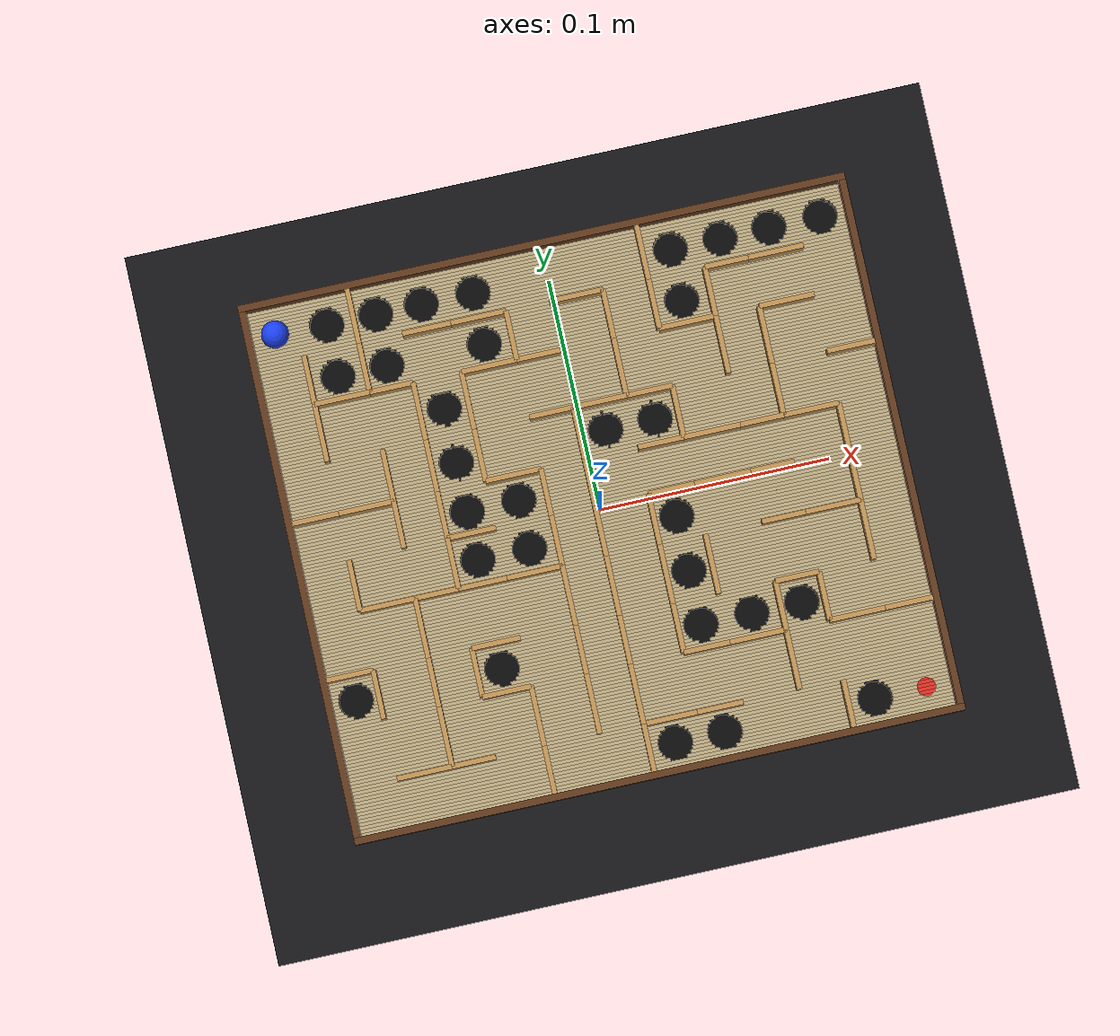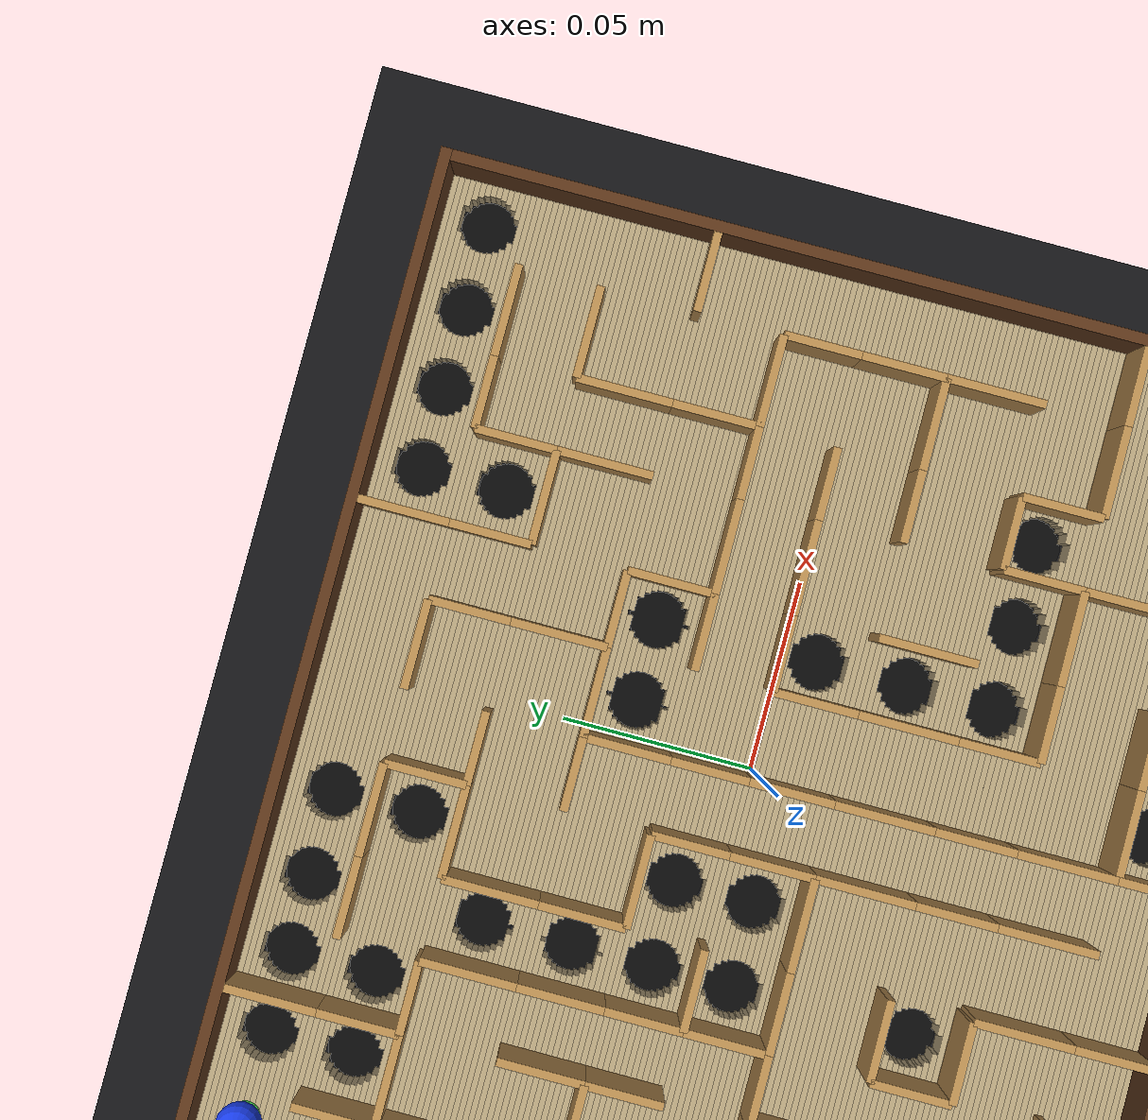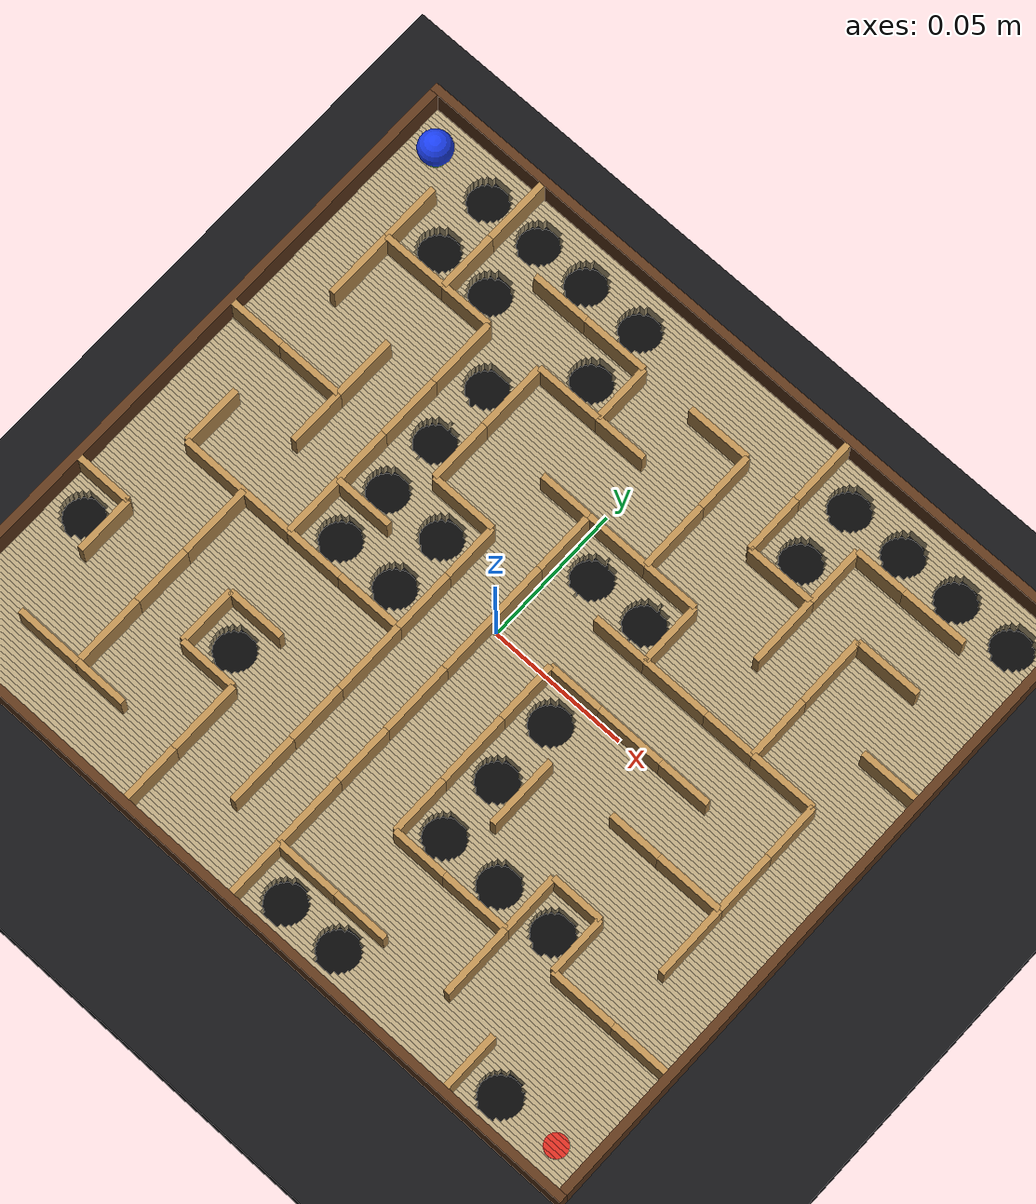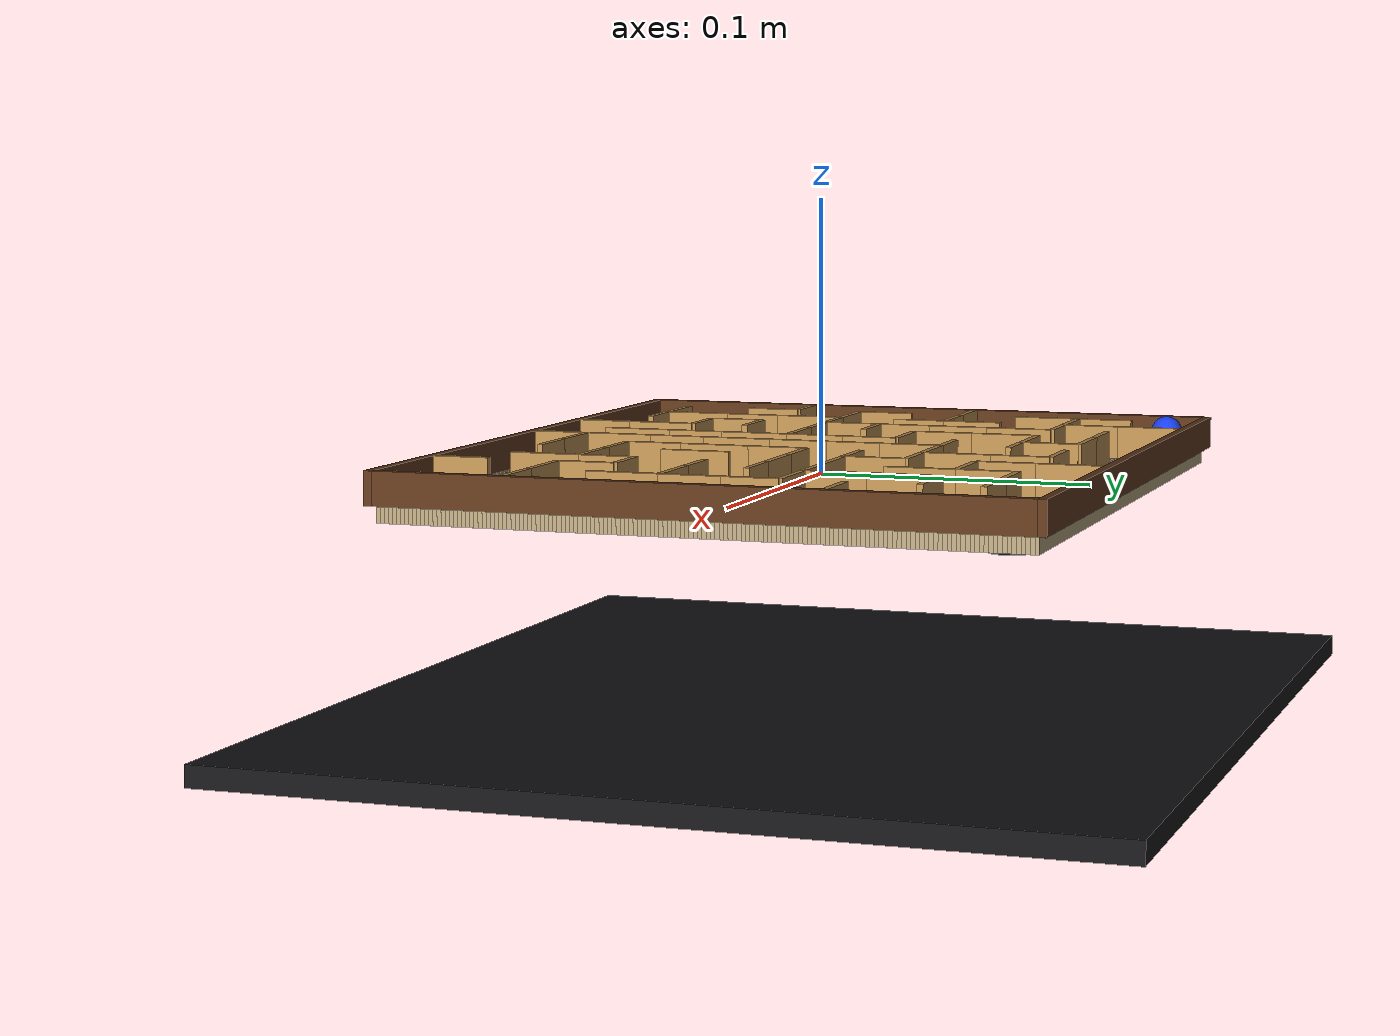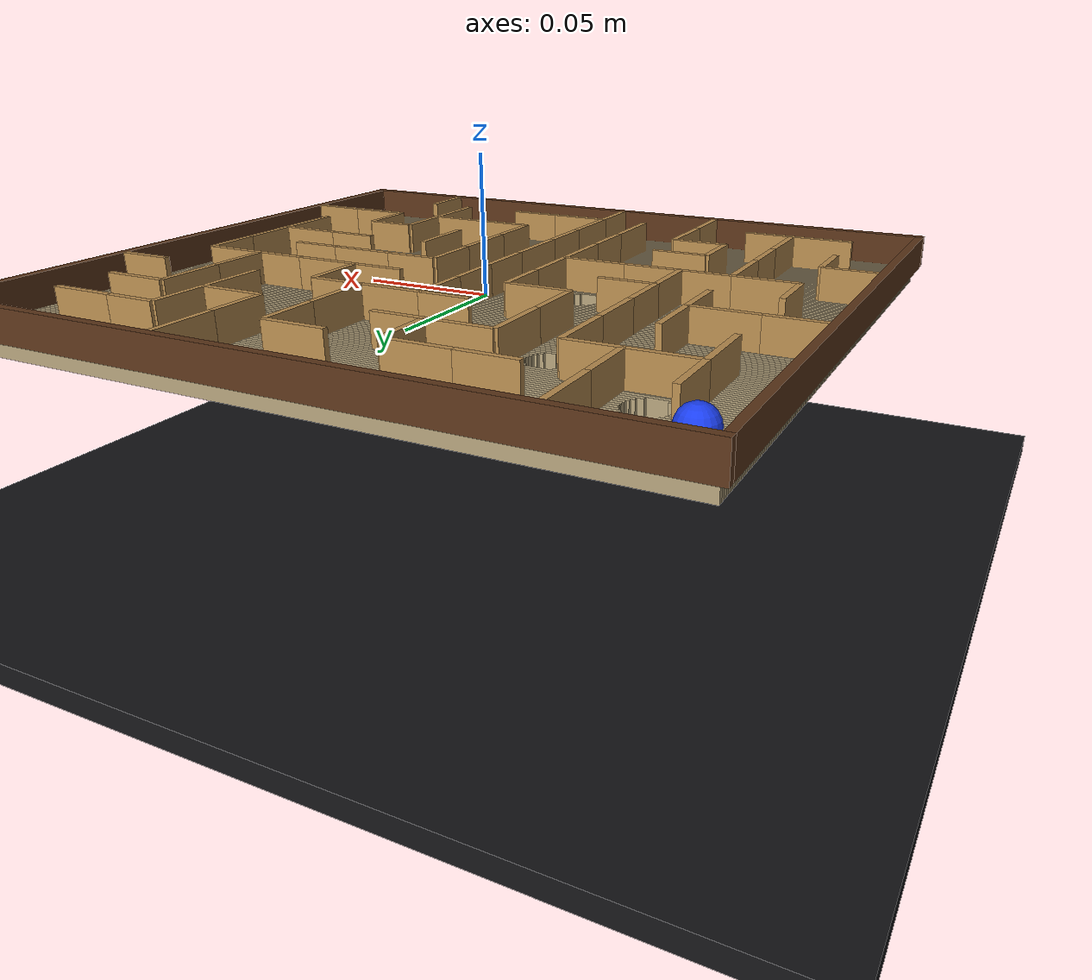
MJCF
<mujoco model="tag_custom_maze">
  <compiler angle="radian" inertiafromgeom="auto"/>
  <option timestep="0.001" gravity="0 0 -9.81" integrator="implicitfast" solver="Newton" iterations="12" tolerance="1e-9"/>
  <size nconmax="4000" njmax="12000"/>
  <visual>
    <global offwidth="900" offheight="800"/>
    <quality shadowsize="2048"/>
    <map znear="0.01" zfar="3"/>
  </visual>
  <default>
    <default class="floor">
      <geom friction="0.30 0.015 0.002" solref="0.004 1" solimp="0.95 0.99 0.001" density="650"/>
    </default>
    <default class="wall">
      <geom friction="0.35 0.02 0.003" solref="0.003 1" solimp="0.95 0.99 0.001" density="700"/>
    </default>
  </default>
  <worldbody>
    <light name="key" pos="0 -0.15 0.55" dir="0 0 -1" diffuse="0.9 0.9 0.9"/>
    <light name="fill" pos="-0.25 0.2 0.35" dir="0.4 -0.3 -1" diffuse="0.45 0.45 0.45"/>
    <camera name="top" pos="0 0 0.43" quat="1 0 0 0" mode="fixed" fovy="37"/>
    <geom name="catch_tray" type="box" pos="0 0 -0.085" size="0.18 0.16 0.004" rgba="0.08 0.08 0.09 1" friction="0.5 0.02 0.003"/>
    <body name="tilt_x_frame" pos="0 0 0">
      <inertial pos="0 0 0" mass="0.02" diaginertia="0.0001 0.0001 0.0001"/>
      <joint name="tilt_x" type="hinge" axis="1 0 0" range="-0.174532925 0.174532925" damping="0.8" armature="0.01"/>
      <body name="board" pos="0 0 0">
        <joint name="tilt_y" type="hinge" axis="0 1 0" range="-0.174532925 0.174532925" damping="0.8" armature="0.01"/>
        <geom name="floor_0" type="box" pos="0 -0.113751634 -0.003" size="0.1295 0.000748366013 0.003" rgba="0.70 0.63 0.48 1" class="floor"/><geom name="floor_1" type="box" pos="0 -0.112254902 -0.003" size="0.1295 0.000748366013 0.003" rgba="0.70 0.63 0.48 1" class="floor"/><geom name="floor_2" type="box" pos="-0.0617699835 -0.11075817 -0.003" size="0.0677300165 0.000748366013 0.003" rgba="0.70 0.63 0.48 1" class="floor"/><geom name="floor_3" type="box" pos="0.0203083257 -0.11075817 -0.003" size="0.00723407496 0.000748366013 0.003" rgba="0.70 0.63 0.48 1" class="floor"/><geom name="floor_4" type="box" pos="0.0638678561 -0.11075817 -0.003" size="0.0292112377 0.000748366013 0.003" rgba="0.70 0.63 0.48 1" class="floor"/><geom name="floor_5" type="box" pos="0.114846656 -0.11075817 -0.003" size="0.0146533442 0.000748366013 0.003" rgba="0.70 0.63 0.48 1" class="floor"/><geom name="floor_6" type="box" pos="-0.0627381572 -0.109261438 -0.003" size="0.0667618428 0.000748366013 0.003" rgba="0.70 0.63 0.48 1" class="floor"/><geom name="floor_7" type="box" pos="0.0203083257 -0.109261438 -0.003" size="0.00529772742 0.000748366013 0.003" rgba="0.70 0.63 0.48 1" class="floor"/><geom name="floor_8" type="box" pos="0.0638678561 -0.109261438 -0.003" size="0.0272748902 0.000748366013 0.003" rgba="0.70 0.63 0.48 1" class="floor"/><geom name="floor_9" type="box" pos="0.11581483 -0.109261438 -0.003" size="0.0136851705 0.000748366013 0.003" rgba="0.70 0.63 0.48 1" class="floor"/><geom name="floor_10" type="box" pos="-0.0632786273 -0.107764706 -0.003" size="0.0662213727 0.000748366013 0.003" rgba="0.70 0.63 0.48 1" class="floor"/><geom name="floor_11" type="box" pos="0.0203083257 -0.107764706 -0.003" size="0.00421678731 0.000748366013 0.003" rgba="0.70 0.63 0.48 1" class="floor"/><geom name="floor_12" type="box" pos="0.0638678561 -0.107764706 -0.003" size="0.0261939501 0.000748366013 0.003" rgba="0.70 0.63 0.48 1" class="floor"/><geom name="floor_13" type="box" pos="0.1163553 -0.107764706 -0.003" size="0.0131447004 0.000748366013 0.003" rgba="0.70 0.63 0.48 1" class="floor"/><geom name="floor_14" type="box" pos="-0.0635895849 -0.106267974 -0.003" size="0.0659104151 0.000748366013 0.003" rgba="0.70 0.63 0.48 1" class="floor"/><geom name="floor_15" type="box" pos="0.0203083257 -0.106267974 -0.003" size="0.00359487212 0.000748366013 0.003" rgba="0.70 0.63 0.48 1" class="floor"/><geom name="floor_16" type="box" pos="0.0638678561 -0.106267974 -0.003" size="0.0255720349 0.000748366013 0.003" rgba="0.70 0.63 0.48 1" class="floor"/><geom name="floor_17" type="box" pos="0.116666257 -0.106267974 -0.003" size="0.0128337428 0.000748366013 0.003" rgba="0.70 0.63 0.48 1" class="floor"/><geom name="floor_18" type="box" pos="-0.0637287644 -0.104771242 -0.003" size="0.0657712356 0.000748366013 0.003" rgba="0.70 0.63 0.48 1" class="floor"/><geom name="floor_19" type="box" pos="0.0203083257 -0.104771242 -0.003" size="0.00331651318 0.000748366013 0.003" rgba="0.70 0.63 0.48 1" class="floor"/><geom name="floor_20" type="box" pos="0.0638678561 -0.104771242 -0.003" size="0.0252936759 0.000748366013 0.003" rgba="0.70 0.63 0.48 1" class="floor"/><geom name="floor_21" type="box" pos="0.116805437 -0.104771242 -0.003" size="0.0126945634 0.000748366013 0.003" rgba="0.70 0.63 0.48 1" class="floor"/><geom name="floor_22" type="box" pos="-0.0637154755 -0.10327451 -0.003" size="0.0657845245 0.000748366013 0.003" rgba="0.70 0.63 0.48 1" class="floor"/><geom name="floor_23" type="box" pos="0.0203083257 -0.10327451 -0.003" size="0.00334309099 0.000748366013 0.003" rgba="0.70 0.63 0.48 1" class="floor"/><geom name="floor_24" type="box" pos="0.0638678561 -0.10327451 -0.003" size="0.0253202538 0.000748366013 0.003" rgba="0.70 0.63 0.48 1" class="floor"/><geom name="floor_25" type="box" pos="0.116792148 -0.10327451 -0.003" size="0.0127078523 0.000748366013 0.003" rgba="0.70 0.63 0.48 1" class="floor"/><geom name="floor_26" type="box" pos="-0.0635480095 -0.101777778 -0.003" size="0.0659519905 0.000748366013 0.003" rgba="0.70 0.63 0.48 1" class="floor"/><geom name="floor_27" type="box" pos="0.0203083257 -0.101777778 -0.003" size="0.00367802285 0.000748366013 0.003" rgba="0.70 0.63 0.48 1" class="floor"/><geom name="floor_28" type="box" pos="0.0638678561 -0.101777778 -0.003" size="0.0256551856 0.000748366013 0.003" rgba="0.70 0.63 0.48 1" class="floor"/><geom name="floor_29" type="box" pos="0.116624682 -0.101777778 -0.003" size="0.0128753182 0.000748366013 0.003" rgba="0.70 0.63 0.48 1" class="floor"/><geom name="floor_30" type="box" pos="-0.063202333 -0.100281046 -0.003" size="0.066297667 0.000748366013 0.003" rgba="0.70 0.63 0.48 1" class="floor"/><geom name="floor_31" type="box" pos="0.0203083257 -0.100281046 -0.003" size="0.00436937586 0.000748366013 0.003" rgba="0.70 0.63 0.48 1" class="floor"/><geom name="floor_32" type="box" pos="0.0638678561 -0.100281046 -0.003" size="0.0263465386 0.000748366013 0.003" rgba="0.70 0.63 0.48 1" class="floor"/><geom name="floor_33" type="box" pos="0.116279005 -0.100281046 -0.003" size="0.0132209947 0.000748366013 0.003" rgba="0.70 0.63 0.48 1" class="floor"/><geom name="floor_34" type="box" pos="-0.0626087637 -0.0987843137 -0.003" size="0.0668912363 0.000748366013 0.003" rgba="0.70 0.63 0.48 1" class="floor"/><geom name="floor_35" type="box" pos="0.0203083257 -0.0987843137 -0.003" size="0.00555651453 0.000748366013 0.003" rgba="0.70 0.63 0.48 1" class="floor"/><geom name="floor_36" type="box" pos="0.0638678561 -0.0987843137 -0.003" size="0.0275336773 0.000748366013 0.003" rgba="0.70 0.63 0.48 1" class="floor"/><geom name="floor_37" type="box" pos="0.115685436 -0.0987843137 -0.003" size="0.013814564 0.000748366013 0.003" rgba="0.70 0.63 0.48 1" class="floor"/><geom name="floor_38" type="box" pos="-0.0614983708 -0.0972875817 -0.003" size="0.0680016292 0.000748366013 0.003" rgba="0.70 0.63 0.48 1" class="floor"/><geom name="floor_39" type="box" pos="0.0203083257 -0.0972875817 -0.003" size="0.00777730028 0.000748366013 0.003" rgba="0.70 0.63 0.48 1" class="floor"/><geom name="floor_40" type="box" pos="0.0638678561 -0.0972875817 -0.003" size="0.029754463 0.000748366013 0.003" rgba="0.70 0.63 0.48 1" class="floor"/><geom name="floor_41" type="box" pos="0.114575043 -0.0972875817 -0.003" size="0.0149249569 0.000748366013 0.003" rgba="0.70 0.63 0.48 1" class="floor"/><geom name="floor_42" type="box" pos="0 -0.0957908497 -0.003" size="0.1295 0.000748366013 0.003" rgba="0.70 0.63 0.48 1" class="floor"/><geom name="floor_43" type="box" pos="0 -0.0942941176 -0.003" size="0.1295 0.000748366013 0.003" rgba="0.70 0.63 0.48 1" class="floor"/><geom name="floor_44" type="box" pos="0 -0.0927973856 -0.003" size="0.1295 0.000748366013 0.003" rgba="0.70 0.63 0.48 1" class="floor"/><geom name="floor_45" type="box" pos="0 -0.0913006536 -0.003" size="0.1295 0.000748366013 0.003" rgba="0.70 0.63 0.48 1" class="floor"/><geom name="floor_46" type="box" pos="0 -0.0898039216 -0.003" size="0.1295 0.000748366013 0.003" rgba="0.70 0.63 0.48 1" class="floor"/><geom name="floor_47" type="box" pos="0 -0.0883071895 -0.003" size="0.1295 0.000748366013 0.003" rgba="0.70 0.63 0.48 1" class="floor"/><geom name="floor_48" type="box" pos="0 -0.0868104575 -0.003" size="0.1295 0.000748366013 0.003" rgba="0.70 0.63 0.48 1" class="floor"/><geom name="floor_49" type="box" pos="0 -0.0853137255 -0.003" size="0.1295 0.000748366013 0.003" rgba="0.70 0.63 0.48 1" class="floor"/><geom name="floor_50" type="box" pos="0 -0.0838169935 -0.003" size="0.1295 0.000748366013 0.003" rgba="0.70 0.63 0.48 1" class="floor"/><geom name="floor_51" type="box" pos="0 -0.0823202614 -0.003" size="0.1295 0.000748366013 0.003" rgba="0.70 0.63 0.48 1" class="floor"/><geom name="floor_52" type="box" pos="0 -0.0808235294 -0.003" size="0.1295 0.000748366013 0.003" rgba="0.70 0.63 0.48 1" class="floor"/><geom name="floor_53" type="box" pos="0 -0.0793267974 -0.003" size="0.1295 0.000748366013 0.003" rgba="0.70 0.63 0.48 1" class="floor"/><geom name="floor_54" type="box" pos="0 -0.0778300654 -0.003" size="0.1295 0.000748366013 0.003" rgba="0.70 0.63 0.48 1" class="floor"/><geom name="floor_55" type="box" pos="0 -0.0763333333 -0.003" size="0.1295 0.000748366013 0.003" rgba="0.70 0.63 0.48 1" class="floor"/><geom name="floor_56" type="box" pos="0 -0.0748366013 -0.003" size="0.1295 0.000748366013 0.003" rgba="0.70 0.63 0.48 1" class="floor"/><geom name="floor_57" type="box" pos="0 -0.0733398693 -0.003" size="0.1295 0.000748366013 0.003" rgba="0.70 0.63 0.48 1" class="floor"/><geom name="floor_58" type="box" pos="0 -0.0718431373 -0.003" size="0.1295 0.000748366013 0.003" rgba="0.70 0.63 0.48 1" class="floor"/><geom name="floor_59" type="box" pos="0 -0.0703464052 -0.003" size="0.1295 0.000748366013 0.003" rgba="0.70 0.63 0.48 1" class="floor"/><geom name="floor_60" type="box" pos="0 -0.0688496732 -0.003" size="0.1295 0.000748366013 0.003" rgba="0.70 0.63 0.48 1" class="floor"/><geom name="floor_61" type="box" pos="0 -0.0673529412 -0.003" size="0.1295 0.000748366013 0.003" rgba="0.70 0.63 0.48 1" class="floor"/><geom name="floor_62" type="box" pos="0 -0.0658562092 -0.003" size="0.1295 0.000748366013 0.003" rgba="0.70 0.63 0.48 1" class="floor"/><geom name="floor_63" type="box" pos="-0.125628628 -0.0643594771 -0.003" size="0.00387137182 0.000748366013 0.003" rgba="0.70 0.63 0.48 1" class="floor"/><geom name="floor_64" type="box" pos="-0.0875934613 -0.0643594771 -0.003" size="0.0293903868 0.000748366013 0.003" rgba="0.70 0.63 0.48 1" class="floor"/><geom name="floor_65" type="box" pos="-0.0123584304 -0.0643594771 -0.003" size="0.0410712359 0.000748366013 0.003" rgba="0.70 0.63 0.48 1" class="floor"/><geom name="floor_66" type="box" pos="0.0422359482 -0.0643594771 -0.003" size="0.00874973455 0.000748366013 0.003" rgba="0.70 0.63 0.48 1" class="floor"/><geom name="floor_67" type="box" pos="0.064260709 -0.0643594771 -0.003" size="0.00850161804 0.000748366013 0.003" rgba="0.70 0.63 0.48 1" class="floor"/><geom name="floor_68" type="box" pos="0.103517868 -0.0643594771 -0.003" size="0.0259821324 0.000748366013 0.003" rgba="0.70 0.63 0.48 1" class="floor"/><geom name="floor_69" type="box" pos="-0.126922242 -0.0628627451 -0.003" size="0.00257775764 0.000748366013 0.003" rgba="0.70 0.63 0.48 1" class="floor"/><geom name="floor_70" type="box" pos="-0.0875934613 -0.0628627451 -0.003" size="0.0268031585 0.000748366013 0.003" rgba="0.70 0.63 0.48 1" class="floor"/><geom name="floor_71" type="box" pos="-0.0123584304 -0.0628627451 -0.003" size="0.0384840075 0.000748366013 0.003" rgba="0.70 0.63 0.48 1" class="floor"/><geom name="floor_72" type="box" pos="0.0422359482 -0.0628627451 -0.003" size="0.0061625062 0.000748366013 0.003" rgba="0.70 0.63 0.48 1" class="floor"/><geom name="floor_73" type="box" pos="0.064260709 -0.0628627451 -0.003" size="0.00591438969 0.000748366013 0.003" rgba="0.70 0.63 0.48 1" class="floor"/><geom name="floor_74" type="box" pos="0.104811482 -0.0628627451 -0.003" size="0.0246885182 0.000748366013 0.003" rgba="0.70 0.63 0.48 1" class="floor"/><geom name="floor_75" type="box" pos="-0.127569891 -0.0613660131 -0.003" size="0.00193010913 0.000748366013 0.003" rgba="0.70 0.63 0.48 1" class="floor"/><geom name="floor_76" type="box" pos="-0.0875934613 -0.0613660131 -0.003" size="0.0255078615 0.000748366013 0.003" rgba="0.70 0.63 0.48 1" class="floor"/><geom name="floor_77" type="box" pos="-0.0123584304 -0.0613660131 -0.003" size="0.0371887105 0.000748366013 0.003" rgba="0.70 0.63 0.48 1" class="floor"/><geom name="floor_78" type="box" pos="0.0422359482 -0.0613660131 -0.003" size="0.00486720918 0.000748366013 0.003" rgba="0.70 0.63 0.48 1" class="floor"/><geom name="floor_79" type="box" pos="0.064260709 -0.0613660131 -0.003" size="0.00461909267 0.000748366013 0.003" rgba="0.70 0.63 0.48 1" class="floor"/><geom name="floor_80" type="box" pos="0.10545913 -0.0613660131 -0.003" size="0.0240408697 0.000748366013 0.003" rgba="0.70 0.63 0.48 1" class="floor"/><geom name="floor_81" type="box" pos="-0.127949037 -0.059869281 -0.003" size="0.00155096311 0.000748366013 0.003" rgba="0.70 0.63 0.48 1" class="floor"/><geom name="floor_82" type="box" pos="-0.0875934613 -0.059869281 -0.003" size="0.0247495694 0.000748366013 0.003" rgba="0.70 0.63 0.48 1" class="floor"/><geom name="floor_83" type="box" pos="-0.0123584304 -0.059869281 -0.003" size="0.0364304184 0.000748366013 0.003" rgba="0.70 0.63 0.48 1" class="floor"/><geom name="floor_84" type="box" pos="0.0422359482 -0.059869281 -0.003" size="0.00410891713 0.000748366013 0.003" rgba="0.70 0.63 0.48 1" class="floor"/><geom name="floor_85" type="box" pos="0.064260709 -0.059869281 -0.003" size="0.00386080062 0.000748366013 0.003" rgba="0.70 0.63 0.48 1" class="floor"/><geom name="floor_86" type="box" pos="0.105838276 -0.059869281 -0.003" size="0.0236617237 0.000748366013 0.003" rgba="0.70 0.63 0.48 1" class="floor"/><geom name="floor_87" type="box" pos="-0.128142987 -0.058372549 -0.003" size="0.00135701346 0.000748366013 0.003" rgba="0.70 0.63 0.48 1" class="floor"/><geom name="floor_88" type="box" pos="-0.0875934613 -0.058372549 -0.003" size="0.0243616701 0.000748366013 0.003" rgba="0.70 0.63 0.48 1" class="floor"/><geom name="floor_89" type="box" pos="-0.0123584304 -0.058372549 -0.003" size="0.0360425192 0.000748366013 0.003" rgba="0.70 0.63 0.48 1" class="floor"/><geom name="floor_90" type="box" pos="0.0422359482 -0.058372549 -0.003" size="0.00372101784 0.000748366013 0.003" rgba="0.70 0.63 0.48 1" class="floor"/><geom name="floor_91" type="box" pos="0.064260709 -0.058372549 -0.003" size="0.00347290134 0.000748366013 0.003" rgba="0.70 0.63 0.48 1" class="floor"/><geom name="floor_92" type="box" pos="0.106032226 -0.058372549 -0.003" size="0.0234677741 0.000748366013 0.003" rgba="0.70 0.63 0.48 1" class="floor"/><geom name="floor_93" type="box" pos="-0.128180622 -0.056875817 -0.003" size="0.00131937811 0.000748366013 0.003" rgba="0.70 0.63 0.48 1" class="floor"/><geom name="floor_94" type="box" pos="-0.0875934613 -0.056875817 -0.003" size="0.0242863994 0.000748366013 0.003" rgba="0.70 0.63 0.48 1" class="floor"/><geom name="floor_95" type="box" pos="-0.0123584304 -0.056875817 -0.003" size="0.0359672485 0.000748366013 0.003" rgba="0.70 0.63 0.48 1" class="floor"/><geom name="floor_96" type="box" pos="0.0422359482 -0.056875817 -0.003" size="0.00364574714 0.000748366013 0.003" rgba="0.70 0.63 0.48 1" class="floor"/><geom name="floor_97" type="box" pos="0.064260709 -0.056875817 -0.003" size="0.00339763064 0.000748366013 0.003" rgba="0.70 0.63 0.48 1" class="floor"/><geom name="floor_98" type="box" pos="0.106069861 -0.056875817 -0.003" size="0.0234301387 0.000748366013 0.003" rgba="0.70 0.63 0.48 1" class="floor"/><geom name="floor_99" type="box" pos="-0.128066806 -0.055379085 -0.003" size="0.00143319391 0.000748366013 0.003" rgba="0.70 0.63 0.48 1" class="floor"/><geom name="floor_100" type="box" pos="-0.0875934613 -0.055379085 -0.003" size="0.024514031 0.000748366013 0.003" rgba="0.70 0.63 0.48 1" class="floor"/><geom name="floor_101" type="box" pos="-0.0123584304 -0.055379085 -0.003" size="0.0361948801 0.000748366013 0.003" rgba="0.70 0.63 0.48 1" class="floor"/><geom name="floor_102" type="box" pos="0.0422359482 -0.055379085 -0.003" size="0.00387337874 0.000748366013 0.003" rgba="0.70 0.63 0.48 1" class="floor"/><geom name="floor_103" type="box" pos="0.064260709 -0.055379085 -0.003" size="0.00362526223 0.000748366013 0.003" rgba="0.70 0.63 0.48 1" class="floor"/><geom name="floor_104" type="box" pos="0.105956046 -0.055379085 -0.003" size="0.0235439545 0.000748366013 0.003" rgba="0.70 0.63 0.48 1" class="floor"/><geom name="floor_105" type="box" pos="-0.127786142 -0.0538823529 -0.003" size="0.00171385809 0.000748366013 0.003" rgba="0.70 0.63 0.48 1" class="floor"/><geom name="floor_106" type="box" pos="-0.0875934613 -0.0538823529 -0.003" size="0.0250753594 0.000748366013 0.003" rgba="0.70 0.63 0.48 1" class="floor"/><geom name="floor_107" type="box" pos="-0.0123584304 -0.0538823529 -0.003" size="0.0367562084 0.000748366013 0.003" rgba="0.70 0.63 0.48 1" class="floor"/><geom name="floor_108" type="box" pos="0.0422359482 -0.0538823529 -0.003" size="0.0044347071 0.000748366013 0.003" rgba="0.70 0.63 0.48 1" class="floor"/><geom name="floor_109" type="box" pos="0.064260709 -0.0538823529 -0.003" size="0.0041865906 0.000748366013 0.003" rgba="0.70 0.63 0.48 1" class="floor"/><geom name="floor_110" type="box" pos="0.105675381 -0.0538823529 -0.003" size="0.0238246187 0.000748366013 0.003" rgba="0.70 0.63 0.48 1" class="floor"/><geom name="floor_111" type="box" pos="-0.127289832 -0.0523856209 -0.003" size="0.00221016792 0.000748366013 0.003" rgba="0.70 0.63 0.48 1" class="floor"/><geom name="floor_112" type="box" pos="-0.0875934613 -0.0523856209 -0.003" size="0.026067979 0.000748366013 0.003" rgba="0.70 0.63 0.48 1" class="floor"/><geom name="floor_113" type="box" pos="-0.0123584304 -0.0523856209 -0.003" size="0.0377488281 0.000748366013 0.003" rgba="0.70 0.63 0.48 1" class="floor"/><geom name="floor_114" type="box" pos="0.0422359482 -0.0523856209 -0.003" size="0.00542732675 0.000748366013 0.003" rgba="0.70 0.63 0.48 1" class="floor"/><geom name="floor_115" type="box" pos="0.064260709 -0.0523856209 -0.003" size="0.00517921024 0.000748366013 0.003" rgba="0.70 0.63 0.48 1" class="floor"/><geom name="floor_116" type="box" pos="0.105179071 -0.0523856209 -0.003" size="0.0243209285 0.000748366013 0.003" rgba="0.70 0.63 0.48 1" class="floor"/><geom name="floor_117" type="box" pos="-0.126422378 -0.0508888889 -0.003" size="0.00307762182 0.000748366013 0.003" rgba="0.70 0.63 0.48 1" class="floor"/><geom name="floor_118" type="box" pos="-0.0875934613 -0.0508888889 -0.003" size="0.0278028868 0.000748366013 0.003" rgba="0.70 0.63 0.48 1" class="floor"/><geom name="floor_119" type="box" pos="-0.0123584304 -0.0508888889 -0.003" size="0.0394837359 0.000748366013 0.003" rgba="0.70 0.63 0.48 1" class="floor"/><geom name="floor_120" type="box" pos="0.0422359482 -0.0508888889 -0.003" size="0.00716223456 0.000748366013 0.003" rgba="0.70 0.63 0.48 1" class="floor"/><geom name="floor_121" type="box" pos="0.064260709 -0.0508888889 -0.003" size="0.00691411805 0.000748366013 0.003" rgba="0.70 0.63 0.48 1" class="floor"/><geom name="floor_122" type="box" pos="0.104311618 -0.0508888889 -0.003" size="0.0251883824 0.000748366013 0.003" rgba="0.70 0.63 0.48 1" class="floor"/><geom name="floor_123" type="box" pos="0 -0.0493921569 -0.003" size="0.1295 0.000748366013 0.003" rgba="0.70 0.63 0.48 1" class="floor"/><geom name="floor_124" type="box" pos="0 -0.0478954248 -0.003" size="0.1295 0.000748366013 0.003" rgba="0.70 0.63 0.48 1" class="floor"/><geom name="floor_125" type="box" pos="0 -0.0463986928 -0.003" size="0.1295 0.000748366013 0.003" rgba="0.70 0.63 0.48 1" class="floor"/><geom name="floor_126" type="box" pos="0 -0.0449019608 -0.003" size="0.1295 0.000748366013 0.003" rgba="0.70 0.63 0.48 1" class="floor"/><geom name="floor_127" type="box" pos="0 -0.0434052288 -0.003" size="0.1295 0.000748366013 0.003" rgba="0.70 0.63 0.48 1" class="floor"/><geom name="floor_128" type="box" pos="0 -0.0419084967 -0.003" size="0.1295 0.000748366013 0.003" rgba="0.70 0.63 0.48 1" class="floor"/><geom name="floor_129" type="box" pos="-0.0508813088 -0.0404117647 -0.003" size="0.0786186912 0.000748366013 0.003" rgba="0.70 0.63 0.48 1" class="floor"/><geom name="floor_130" type="box" pos="0.0819808183 -0.0404117647 -0.003" size="0.0475191817 0.000748366013 0.003" rgba="0.70 0.63 0.48 1" class="floor"/><geom name="floor_131" type="box" pos="-0.0518989685 -0.0389150327 -0.003" size="0.0776010315 0.000748366013 0.003" rgba="0.70 0.63 0.48 1" class="floor"/><geom name="floor_132" type="box" pos="0.0829984781 -0.0389150327 -0.003" size="0.0465015219 0.000748366013 0.003" rgba="0.70 0.63 0.48 1" class="floor"/><geom name="floor_133" type="box" pos="-0.0524591004 -0.0374183007 -0.003" size="0.0770408996 0.000748366013 0.003" rgba="0.70 0.63 0.48 1" class="floor"/><geom name="floor_134" type="box" pos="0.0835586099 -0.0374183007 -0.003" size="0.0459413901 0.000748366013 0.003" rgba="0.70 0.63 0.48 1" class="floor"/><geom name="floor_135" type="box" pos="-0.05278313 -0.0359215686 -0.003" size="0.07671687 0.000748366013 0.003" rgba="0.70 0.63 0.48 1" class="floor"/><geom name="floor_136" type="box" pos="0.0838826395 -0.0359215686 -0.003" size="0.0456173605 0.000748366013 0.003" rgba="0.70 0.63 0.48 1" class="floor"/><geom name="floor_137" type="box" pos="-0.0529330573 -0.0344248366 -0.003" size="0.0765669427 0.000748366013 0.003" rgba="0.70 0.63 0.48 1" class="floor"/><geom name="floor_138" type="box" pos="0.0840325668 -0.0344248366 -0.003" size="0.0454674332 0.000748366013 0.003" rgba="0.70 0.63 0.48 1" class="floor"/><geom name="floor_139" type="box" pos="-0.0529299376 -0.0329281046 -0.003" size="0.0765700624 0.000748366013 0.003" rgba="0.70 0.63 0.48 1" class="floor"/><geom name="floor_140" type="box" pos="0.0840294471 -0.0329281046 -0.003" size="0.0454705529 0.000748366013 0.003" rgba="0.70 0.63 0.48 1" class="floor"/><geom name="floor_141" type="box" pos="-0.05277337 -0.0314313725 -0.003" size="0.07672663 0.000748366013 0.003" rgba="0.70 0.63 0.48 1" class="floor"/><geom name="floor_142" type="box" pos="0.0838728795 -0.0314313725 -0.003" size="0.0456271205 0.000748366013 0.003" rgba="0.70 0.63 0.48 1" class="floor"/><geom name="floor_143" type="box" pos="-0.0524411916 -0.0299346405 -0.003" size="0.0770588084 0.000748366013 0.003" rgba="0.70 0.63 0.48 1" class="floor"/><geom name="floor_144" type="box" pos="0.0835407011 -0.0299346405 -0.003" size="0.0459592989 0.000748366013 0.003" rgba="0.70 0.63 0.48 1" class="floor"/><geom name="floor_145" type="box" pos="-0.0518686047 -0.0284379085 -0.003" size="0.0776313953 0.000748366013 0.003" rgba="0.70 0.63 0.48 1" class="floor"/><geom name="floor_146" type="box" pos="0.0829681142 -0.0284379085 -0.003" size="0.0465318858 0.000748366013 0.003" rgba="0.70 0.63 0.48 1" class="floor"/><geom name="floor_147" type="box" pos="-0.0508177891 -0.0269411765 -0.003" size="0.0786822109 0.000748366013 0.003" rgba="0.70 0.63 0.48 1" class="floor"/><geom name="floor_148" type="box" pos="0.0819172986 -0.0269411765 -0.003" size="0.0475827014 0.000748366013 0.003" rgba="0.70 0.63 0.48 1" class="floor"/><geom name="floor_149" type="box" pos="0 -0.0254444444 -0.003" size="0.1295 0.000748366013 0.003" rgba="0.70 0.63 0.48 1" class="floor"/><geom name="floor_150" type="box" pos="0 -0.0239477124 -0.003" size="0.1295 0.000748366013 0.003" rgba="0.70 0.63 0.48 1" class="floor"/><geom name="floor_151" type="box" pos="0 -0.0224509804 -0.003" size="0.1295 0.000748366013 0.003" rgba="0.70 0.63 0.48 1" class="floor"/><geom name="floor_152" type="box" pos="0 -0.0209542484 -0.003" size="0.1295 0.000748366013 0.003" rgba="0.70 0.63 0.48 1" class="floor"/><geom name="floor_153" type="box" pos="0 -0.0194575163 -0.003" size="0.1295 0.000748366013 0.003" rgba="0.70 0.63 0.48 1" class="floor"/><geom name="floor_154" type="box" pos="0 -0.0179607843 -0.003" size="0.1295 0.000748366013 0.003" rgba="0.70 0.63 0.48 1" class="floor"/><geom name="floor_155" type="box" pos="-0.0943162224 -0.0164640523 -0.003" size="0.0351837776 0.000748366013 0.003" rgba="0.70 0.63 0.48 1" class="floor"/><geom name="floor_156" type="box" pos="-0.0445188244 -0.0164640523 -0.003" size="0.0079814716 0.000748366013 0.003" rgba="0.70 0.63 0.48 1" class="floor"/><geom name="floor_157" type="box" pos="-0.00106088439 -0.0164640523 -0.003" size="0.0288443195 0.000748366013 0.003" rgba="0.70 0.63 0.48 1" class="floor"/><geom name="floor_158" type="box" pos="0.081957792 -0.0164640523 -0.003" size="0.047542208 0.000748366013 0.003" rgba="0.70 0.63 0.48 1" class="floor"/><geom name="floor_159" type="box" pos="-0.0953458154 -0.0149673203 -0.003" size="0.0341541846 0.000748366013 0.003" rgba="0.70 0.63 0.48 1" class="floor"/><geom name="floor_160" type="box" pos="-0.0445188244 -0.0149673203 -0.003" size="0.00592228558 0.000748366013 0.003" rgba="0.70 0.63 0.48 1" class="floor"/><geom name="floor_161" type="box" pos="-0.00106088439 -0.0149673203 -0.003" size="0.0267851334 0.000748366013 0.003" rgba="0.70 0.63 0.48 1" class="floor"/><geom name="floor_162" type="box" pos="0.082987385 -0.0149673203 -0.003" size="0.046512615 0.000748366013 0.003" rgba="0.70 0.63 0.48 1" class="floor"/><geom name="floor_163" type="box" pos="-0.0959104954 -0.0134705882 -0.003" size="0.0335895046 0.000748366013 0.003" rgba="0.70 0.63 0.48 1" class="floor"/><geom name="floor_164" type="box" pos="-0.0445188244 -0.0134705882 -0.003" size="0.00479292562 0.000748366013 0.003" rgba="0.70 0.63 0.48 1" class="floor"/><geom name="floor_165" type="box" pos="-0.00106088439 -0.0134705882 -0.003" size="0.0256557735 0.000748366013 0.003" rgba="0.70 0.63 0.48 1" class="floor"/><geom name="floor_166" type="box" pos="0.083552065 -0.0134705882 -0.003" size="0.045947935 0.000748366013 0.003" rgba="0.70 0.63 0.48 1" class="floor"/><geom name="floor_167" type="box" pos="-0.0962375125 -0.0119738562 -0.003" size="0.0332624875 0.000748366013 0.003" rgba="0.70 0.63 0.48 1" class="floor"/><geom name="floor_168" type="box" pos="-0.0445188244 -0.0119738562 -0.003" size="0.00413889148 0.000748366013 0.003" rgba="0.70 0.63 0.48 1" class="floor"/><geom name="floor_169" type="box" pos="-0.00106088439 -0.0119738562 -0.003" size="0.0250017393 0.000748366013 0.003" rgba="0.70 0.63 0.48 1" class="floor"/><geom name="floor_170" type="box" pos="0.083879082 -0.0119738562 -0.003" size="0.045620918 0.000748366013 0.003" rgba="0.70 0.63 0.48 1" class="floor"/><geom name="floor_171" type="box" pos="-0.0963898795 -0.0104771242 -0.003" size="0.0331101205 0.000748366013 0.003" rgba="0.70 0.63 0.48 1" class="floor"/><geom name="floor_172" type="box" pos="-0.0445188244 -0.0104771242 -0.003" size="0.0038341574 0.000748366013 0.003" rgba="0.70 0.63 0.48 1" class="floor"/><geom name="floor_173" type="box" pos="-0.00106088439 -0.0104771242 -0.003" size="0.0246970053 0.000748366013 0.003" rgba="0.70 0.63 0.48 1" class="floor"/><geom name="floor_174" type="box" pos="0.0840314491 -0.0104771242 -0.003" size="0.0454685509 0.000748366013 0.003" rgba="0.70 0.63 0.48 1" class="floor"/><geom name="floor_175" type="box" pos="-0.0963890561 -0.00898039216 -0.003" size="0.0331109439 0.000748366013 0.003" rgba="0.70 0.63 0.48 1" class="floor"/><geom name="floor_176" type="box" pos="-0.0445188244 -0.00898039216 -0.003" size="0.0038358042 0.000748366013 0.003" rgba="0.70 0.63 0.48 1" class="floor"/><geom name="floor_177" type="box" pos="-0.00106088439 -0.00898039216 -0.003" size="0.024698652 0.000748366013 0.003" rgba="0.70 0.63 0.48 1" class="floor"/><geom name="floor_178" type="box" pos="0.0840306257 -0.00898039216 -0.003" size="0.0454693743 0.000748366013 0.003" rgba="0.70 0.63 0.48 1" class="floor"/><geom name="floor_179" type="box" pos="-0.0962349365 -0.00748366013 -0.003" size="0.0332650635 0.000748366013 0.003" rgba="0.70 0.63 0.48 1" class="floor"/><geom name="floor_180" type="box" pos="-0.0445188244 -0.00748366013 -0.003" size="0.00414404346 0.000748366013 0.003" rgba="0.70 0.63 0.48 1" class="floor"/><geom name="floor_181" type="box" pos="-0.00106088439 -0.00748366013 -0.003" size="0.0250068913 0.000748366013 0.003" rgba="0.70 0.63 0.48 1" class="floor"/><geom name="floor_182" type="box" pos="0.0838765061 -0.00748366013 -0.003" size="0.0456234939 0.000748366013 0.003" rgba="0.70 0.63 0.48 1" class="floor"/><geom name="floor_183" type="box" pos="-0.0959057687 -0.0059869281 -0.003" size="0.0335942313 0.000748366013 0.003" rgba="0.70 0.63 0.48 1" class="floor"/><geom name="floor_184" type="box" pos="-0.0445188244 -0.0059869281 -0.003" size="0.00480237911 0.000748366013 0.003" rgba="0.70 0.63 0.48 1" class="floor"/><geom name="floor_185" type="box" pos="-0.00106088439 -0.0059869281 -0.003" size="0.025665227 0.000748366013 0.003" rgba="0.70 0.63 0.48 1" class="floor"/><geom name="floor_186" type="box" pos="0.0835473382 -0.0059869281 -0.003" size="0.0459526618 0.000748366013 0.003" rgba="0.70 0.63 0.48 1" class="floor"/><geom name="floor_187" type="box" pos="-0.0953378015 -0.00449019608 -0.003" size="0.0341621985 0.000748366013 0.003" rgba="0.70 0.63 0.48 1" class="floor"/><geom name="floor_188" type="box" pos="-0.0445188244 -0.00449019608 -0.003" size="0.00593831343 0.000748366013 0.003" rgba="0.70 0.63 0.48 1" class="floor"/><geom name="floor_189" type="box" pos="-0.00106088439 -0.00449019608 -0.003" size="0.0268011613 0.000748366013 0.003" rgba="0.70 0.63 0.48 1" class="floor"/><geom name="floor_190" type="box" pos="0.0829793711 -0.00449019608 -0.003" size="0.0465206289 0.000748366013 0.003" rgba="0.70 0.63 0.48 1" class="floor"/><geom name="floor_191" type="box" pos="-0.0942994608 -0.00299346405 -0.003" size="0.0352005392 0.000748366013 0.003" rgba="0.70 0.63 0.48 1" class="floor"/><geom name="floor_192" type="box" pos="-0.0445188244 -0.00299346405 -0.003" size="0.00801499497 0.000748366013 0.003" rgba="0.70 0.63 0.48 1" class="floor"/><geom name="floor_193" type="box" pos="-0.00106088439 -0.00299346405 -0.003" size="0.0288778428 0.000748366013 0.003" rgba="0.70 0.63 0.48 1" class="floor"/><geom name="floor_194" type="box" pos="0.0819410303 -0.00299346405 -0.003" size="0.0475589697 0.000748366013 0.003" rgba="0.70 0.63 0.48 1" class="floor"/><geom name="floor_195" type="box" pos="0 -0.00149673203 -0.003" size="0.1295 0.000748366013 0.003" rgba="0.70 0.63 0.48 1" class="floor"/><geom name="floor_196" type="box" pos="0 -1.38777878e-17 -0.003" size="0.1295 0.000748366013 0.003" rgba="0.70 0.63 0.48 1" class="floor"/><geom name="floor_197" type="box" pos="0 0.00149673203 -0.003" size="0.1295 0.000748366013 0.003" rgba="0.70 0.63 0.48 1" class="floor"/><geom name="floor_198" type="box" pos="0 0.00299346405 -0.003" size="0.1295 0.000748366013 0.003" rgba="0.70 0.63 0.48 1" class="floor"/><geom name="floor_199" type="box" pos="-0.0940689392 0.00449019608 -0.003" size="0.0354310608 0.000748366013 0.003" rgba="0.70 0.63 0.48 1" class="floor"/><geom name="floor_200" type="box" pos="-0.0445188244 0.00449019608 -0.003" size="0.00847603805 0.000748366013 0.003" rgba="0.70 0.63 0.48 1" class="floor"/><geom name="floor_201" type="box" pos="0.0495501149 0.00449019608 -0.003" size="0.0799498851 0.000748366013 0.003" rgba="0.70 0.63 0.48 1" class="floor"/><geom name="floor_202" type="box" pos="-0.0952331798 0.0059869281 -0.003" size="0.0342668202 0.000748366013 0.003" rgba="0.70 0.63 0.48 1" class="floor"/><geom name="floor_203" type="box" pos="-0.0445188244 0.0059869281 -0.003" size="0.00614755691 0.000748366013 0.003" rgba="0.70 0.63 0.48 1" class="floor"/><geom name="floor_204" type="box" pos="0.0507143554 0.0059869281 -0.003" size="0.0787856446 0.000748366013 0.003" rgba="0.70 0.63 0.48 1" class="floor"/><geom name="floor_205" type="box" pos="-0.0958442272 0.00748366013 -0.003" size="0.0336557728 0.000748366013 0.003" rgba="0.70 0.63 0.48 1" class="floor"/><geom name="floor_206" type="box" pos="-0.0445188244 0.00748366013 -0.003" size="0.00492546198 0.000748366013 0.003" rgba="0.70 0.63 0.48 1" class="floor"/><geom name="floor_207" type="box" pos="0.0513254029 0.00748366013 -0.003" size="0.0781745971 0.000748366013 0.003" rgba="0.70 0.63 0.48 1" class="floor"/><geom name="floor_208" type="box" pos="-0.0962009281 0.00898039216 -0.003" size="0.0332990719 0.000748366013 0.003" rgba="0.70 0.63 0.48 1" class="floor"/><geom name="floor_209" type="box" pos="-0.0445188244 0.00898039216 -0.003" size="0.00421206024 0.000748366013 0.003" rgba="0.70 0.63 0.48 1" class="floor"/><geom name="floor_210" type="box" pos="0.0516821038 0.00898039216 -0.003" size="0.0778178962 0.000748366013 0.003" rgba="0.70 0.63 0.48 1" class="floor"/><geom name="floor_211" type="box" pos="-0.0963772022 0.0104771242 -0.003" size="0.0331227978 0.000748366013 0.003" rgba="0.70 0.63 0.48 1" class="floor"/><geom name="floor_212" type="box" pos="-0.0445188244 0.0104771242 -0.003" size="0.00385951207 0.000748366013 0.003" rgba="0.70 0.63 0.48 1" class="floor"/><geom name="floor_213" type="box" pos="0.0518583778 0.0104771242 -0.003" size="0.0776416222 0.000748366013 0.003" rgba="0.70 0.63 0.48 1" class="floor"/><geom name="floor_214" type="box" pos="-0.0963986456 0.0119738562 -0.003" size="0.0331013544 0.000748366013 0.003" rgba="0.70 0.63 0.48 1" class="floor"/><geom name="floor_215" type="box" pos="-0.0445188244 0.0119738562 -0.003" size="0.00381662524 0.000748366013 0.003" rgba="0.70 0.63 0.48 1" class="floor"/><geom name="floor_216" type="box" pos="0.0518798213 0.0119738562 -0.003" size="0.0776201787 0.000748366013 0.003" rgba="0.70 0.63 0.48 1" class="floor"/><geom name="floor_217" type="box" pos="-0.0962680186 0.0134705882 -0.003" size="0.0332319814 0.000748366013 0.003" rgba="0.70 0.63 0.48 1" class="floor"/><geom name="floor_218" type="box" pos="-0.0445188244 0.0134705882 -0.003" size="0.0040778792 0.000748366013 0.003" rgba="0.70 0.63 0.48 1" class="floor"/><geom name="floor_219" type="box" pos="0.0517491943 0.0134705882 -0.003" size="0.0777508057 0.000748366013 0.003" rgba="0.70 0.63 0.48 1" class="floor"/><geom name="floor_220" type="box" pos="-0.0959673614 0.0149673203 -0.003" size="0.0335326386 0.000748366013 0.003" rgba="0.70 0.63 0.48 1" class="floor"/><geom name="floor_221" type="box" pos="-0.0445188244 0.0149673203 -0.003" size="0.0046791936 0.000748366013 0.003" rgba="0.70 0.63 0.48 1" class="floor"/><geom name="floor_222" type="box" pos="0.0514485371 0.0149673203 -0.003" size="0.0780514629 0.000748366013 0.003" rgba="0.70 0.63 0.48 1" class="floor"/><geom name="floor_223" type="box" pos="-0.0954421202 0.0164640523 -0.003" size="0.0340578798 0.000748366013 0.003" rgba="0.70 0.63 0.48 1" class="floor"/><geom name="floor_224" type="box" pos="-0.0445188244 0.0164640523 -0.003" size="0.00572967613 0.000748366013 0.003" rgba="0.70 0.63 0.48 1" class="floor"/><geom name="floor_225" type="box" pos="0.0509232958 0.0164640523 -0.003" size="0.0785767042 0.000748366013 0.003" rgba="0.70 0.63 0.48 1" class="floor"/><geom name="floor_226" type="box" pos="-0.0945101671 0.0179607843 -0.003" size="0.0349898329 0.000748366013 0.003" rgba="0.70 0.63 0.48 1" class="floor"/><geom name="floor_227" type="box" pos="-0.0445188244 0.0179607843 -0.003" size="0.00759358221 0.000748366013 0.003" rgba="0.70 0.63 0.48 1" class="floor"/><geom name="floor_228" type="box" pos="0.0499913428 0.0179607843 -0.003" size="0.0795086572 0.000748366013 0.003" rgba="0.70 0.63 0.48 1" class="floor"/><geom name="floor_229" type="box" pos="0 0.0194575163 -0.003" size="0.1295 0.000748366013 0.003" rgba="0.70 0.63 0.48 1" class="floor"/><geom name="floor_230" type="box" pos="0 0.0209542484 -0.003" size="0.1295 0.000748366013 0.003" rgba="0.70 0.63 0.48 1" class="floor"/><geom name="floor_231" type="box" pos="0 0.0224509804 -0.003" size="0.1295 0.000748366013 0.003" rgba="0.70 0.63 0.48 1" class="floor"/><geom name="floor_232" type="box" pos="0 0.0239477124 -0.003" size="0.1295 0.000748366013 0.003" rgba="0.70 0.63 0.48 1" class="floor"/><geom name="floor_233" type="box" pos="-0.0928730737 0.0254444444 -0.003" size="0.0366269263 0.000748366013 0.003" rgba="0.70 0.63 0.48 1" class="floor"/><geom name="floor_234" type="box" pos="-0.0231496143 0.0254444444 -0.003" size="0.0322369791 0.000748366013 0.003" rgba="0.70 0.63 0.48 1" class="floor"/><geom name="floor_235" type="box" pos="0.0203083257 0.0254444444 -0.003" size="0.0103614068 0.000748366013 0.003" rgba="0.70 0.63 0.48 1" class="floor"/><geom name="floor_236" type="box" pos="0.0805146433 0.0254444444 -0.003" size="0.0489853567 0.000748366013 0.003" rgba="0.70 0.63 0.48 1" class="floor"/><geom name="floor_237" type="box" pos="-0.0949142099 0.0269411765 -0.003" size="0.0345857901 0.000748366013 0.003" rgba="0.70 0.63 0.48 1" class="floor"/><geom name="floor_238" type="box" pos="-0.0231496143 0.0269411765 -0.003" size="0.0281547067 0.000748366013 0.003" rgba="0.70 0.63 0.48 1" class="floor"/><geom name="floor_239" type="box" pos="0.0203083257 0.0269411765 -0.003" size="0.00627913433 0.000748366013 0.003" rgba="0.70 0.63 0.48 1" class="floor"/><geom name="floor_240" type="box" pos="0.0825557795 0.0269411765 -0.003" size="0.0469442205 0.000748366013 0.003" rgba="0.70 0.63 0.48 1" class="floor"/><geom name="floor_241" type="box" pos="-0.0956603536 0.0284379085 -0.003" size="0.0338396464 0.000748366013 0.003" rgba="0.70 0.63 0.48 1" class="floor"/><geom name="floor_242" type="box" pos="-0.0231496143 0.0284379085 -0.003" size="0.0266624195 0.000748366013 0.003" rgba="0.70 0.63 0.48 1" class="floor"/><geom name="floor_243" type="box" pos="0.0203083257 0.0284379085 -0.003" size="0.00478684711 0.000748366013 0.003" rgba="0.70 0.63 0.48 1" class="floor"/><geom name="floor_244" type="box" pos="0.0833019231 0.0284379085 -0.003" size="0.0461980769 0.000748366013 0.003" rgba="0.70 0.63 0.48 1" class="floor"/><geom name="floor_245" type="box" pos="-0.0960956666 0.0299346405 -0.003" size="0.0334043334 0.000748366013 0.003" rgba="0.70 0.63 0.48 1" class="floor"/><geom name="floor_246" type="box" pos="-0.0231496143 0.0299346405 -0.003" size="0.0257917933 0.000748366013 0.003" rgba="0.70 0.63 0.48 1" class="floor"/><geom name="floor_247" type="box" pos="0.0203083257 0.0299346405 -0.003" size="0.00391622095 0.000748366013 0.003" rgba="0.70 0.63 0.48 1" class="floor"/><geom name="floor_248" type="box" pos="0.0837372362 0.0299346405 -0.003" size="0.0457627638 0.000748366013 0.003" rgba="0.70 0.63 0.48 1" class="floor"/><geom name="floor_249" type="box" pos="-0.0963323435 0.0314313725 -0.003" size="0.0331676565 0.000748366013 0.003" rgba="0.70 0.63 0.48 1" class="floor"/><geom name="floor_250" type="box" pos="-0.0231496143 0.0314313725 -0.003" size="0.0253184396 0.000748366013 0.003" rgba="0.70 0.63 0.48 1" class="floor"/><geom name="floor_251" type="box" pos="0.0203083257 0.0314313725 -0.003" size="0.00344286728 0.000748366013 0.003" rgba="0.70 0.63 0.48 1" class="floor"/><geom name="floor_252" type="box" pos="0.083973913 0.0314313725 -0.003" size="0.045526087 0.000748366013 0.003" rgba="0.70 0.63 0.48 1" class="floor"/><geom name="floor_253" type="box" pos="-0.0964081847 0.0329281046 -0.003" size="0.0330918153 0.000748366013 0.003" rgba="0.70 0.63 0.48 1" class="floor"/><geom name="floor_254" type="box" pos="-0.0231496143 0.0329281046 -0.003" size="0.0251667572 0.000748366013 0.003" rgba="0.70 0.63 0.48 1" class="floor"/><geom name="floor_255" type="box" pos="0.0203083257 0.0329281046 -0.003" size="0.00329118488 0.000748366013 0.003" rgba="0.70 0.63 0.48 1" class="floor"/><geom name="floor_256" type="box" pos="0.0840497542 0.0329281046 -0.003" size="0.0454502458 0.000748366013 0.003" rgba="0.70 0.63 0.48 1" class="floor"/><geom name="floor_257" type="box" pos="-0.0963331613 0.0344248366 -0.003" size="0.0331668387 0.000748366013 0.003" rgba="0.70 0.63 0.48 1" class="floor"/><geom name="floor_258" type="box" pos="-0.0231496143 0.0344248366 -0.003" size="0.0253168039 0.000748366013 0.003" rgba="0.70 0.63 0.48 1" class="floor"/><geom name="floor_259" type="box" pos="0.0203083257 0.0344248366 -0.003" size="0.00344123153 0.000748366013 0.003" rgba="0.70 0.63 0.48 1" class="floor"/><geom name="floor_260" type="box" pos="0.0839747309 0.0344248366 -0.003" size="0.0455252691 0.000748366013 0.003" rgba="0.70 0.63 0.48 1" class="floor"/><geom name="floor_261" type="box" pos="-0.0960974148 0.0359215686 -0.003" size="0.0334025852 0.000748366013 0.003" rgba="0.70 0.63 0.48 1" class="floor"/><geom name="floor_262" type="box" pos="-0.0231496143 0.0359215686 -0.003" size="0.0257882971 0.000748366013 0.003" rgba="0.70 0.63 0.48 1" class="floor"/><geom name="floor_263" type="box" pos="0.0203083257 0.0359215686 -0.003" size="0.00391272471 0.000748366013 0.003" rgba="0.70 0.63 0.48 1" class="floor"/><geom name="floor_264" type="box" pos="0.0837389843 0.0359215686 -0.003" size="0.0457610157 0.000748366013 0.003" rgba="0.70 0.63 0.48 1" class="floor"/><geom name="floor_265" type="box" pos="-0.0956633552 0.0374183007 -0.003" size="0.0338366448 0.000748366013 0.003" rgba="0.70 0.63 0.48 1" class="floor"/><geom name="floor_266" type="box" pos="-0.0231496143 0.0374183007 -0.003" size="0.0266564162 0.000748366013 0.003" rgba="0.70 0.63 0.48 1" class="floor"/><geom name="floor_267" type="box" pos="0.0203083257 0.0374183007 -0.003" size="0.00478084379 0.000748366013 0.003" rgba="0.70 0.63 0.48 1" class="floor"/><geom name="floor_268" type="box" pos="0.0833049248 0.0374183007 -0.003" size="0.0461950752 0.000748366013 0.003" rgba="0.70 0.63 0.48 1" class="floor"/><geom name="floor_269" type="box" pos="-0.0949195322 0.0389150327 -0.003" size="0.0345804678 0.000748366013 0.003" rgba="0.70 0.63 0.48 1" class="floor"/><geom name="floor_270" type="box" pos="-0.0231496143 0.0389150327 -0.003" size="0.0281440622 0.000748366013 0.003" rgba="0.70 0.63 0.48 1" class="floor"/><geom name="floor_271" type="box" pos="0.0203083257 0.0389150327 -0.003" size="0.0062684898 0.000748366013 0.003" rgba="0.70 0.63 0.48 1" class="floor"/><geom name="floor_272" type="box" pos="0.0825611018 0.0389150327 -0.003" size="0.0469388982 0.000748366013 0.003" rgba="0.70 0.63 0.48 1" class="floor"/><geom name="floor_273" type="box" pos="-0.0929342837 0.0404117647 -0.003" size="0.0365657163 0.000748366013 0.003" rgba="0.70 0.63 0.48 1" class="floor"/><geom name="floor_274" type="box" pos="-0.0231496143 0.0404117647 -0.003" size="0.0321145591 0.000748366013 0.003" rgba="0.70 0.63 0.48 1" class="floor"/><geom name="floor_275" type="box" pos="0.0203083257 0.0404117647 -0.003" size="0.0102389868 0.000748366013 0.003" rgba="0.70 0.63 0.48 1" class="floor"/><geom name="floor_276" type="box" pos="0.0805758533 0.0404117647 -0.003" size="0.0489241467 0.000748366013 0.003" rgba="0.70 0.63 0.48 1" class="floor"/><geom name="floor_277" type="box" pos="0 0.0419084967 -0.003" size="0.1295 0.000748366013 0.003" rgba="0.70 0.63 0.48 1" class="floor"/><geom name="floor_278" type="box" pos="0 0.0434052288 -0.003" size="0.1295 0.000748366013 0.003" rgba="0.70 0.63 0.48 1" class="floor"/><geom name="floor_279" type="box" pos="0 0.0449019608 -0.003" size="0.1295 0.000748366013 0.003" rgba="0.70 0.63 0.48 1" class="floor"/><geom name="floor_280" type="box" pos="0 0.0463986928 -0.003" size="0.1295 0.000748366013 0.003" rgba="0.70 0.63 0.48 1" class="floor"/><geom name="floor_281" type="box" pos="0 0.0478954248 -0.003" size="0.1295 0.000748366013 0.003" rgba="0.70 0.63 0.48 1" class="floor"/><geom name="floor_282" type="box" pos="-0.093272601 0.0493921569 -0.003" size="0.036227399 0.000748366013 0.003" rgba="0.70 0.63 0.48 1" class="floor"/><geom name="floor_283" type="box" pos="0.0374562305 0.0493921569 -0.003" size="0.0920437695 0.000748366013 0.003" rgba="0.70 0.63 0.48 1" class="floor"/><geom name="floor_284" type="box" pos="-0.0949721322 0.0508888889 -0.003" size="0.0345278678 0.000748366013 0.003" rgba="0.70 0.63 0.48 1" class="floor"/><geom name="floor_285" type="box" pos="0.0391557618 0.0508888889 -0.003" size="0.0903442382 0.000748366013 0.003" rgba="0.70 0.63 0.48 1" class="floor"/><geom name="floor_286" type="box" pos="-0.0956931632 0.0523856209 -0.003" size="0.0338068368 0.000748366013 0.003" rgba="0.70 0.63 0.48 1" class="floor"/><geom name="floor_287" type="box" pos="0.0398767928 0.0523856209 -0.003" size="0.0896232072 0.000748366013 0.003" rgba="0.70 0.63 0.48 1" class="floor"/><geom name="floor_288" type="box" pos="-0.0961147339 0.0538823529 -0.003" size="0.0333852661 0.000748366013 0.003" rgba="0.70 0.63 0.48 1" class="floor"/><geom name="floor_289" type="box" pos="0.0402983635 0.0538823529 -0.003" size="0.0892016365 0.000748366013 0.003" rgba="0.70 0.63 0.48 1" class="floor"/><geom name="floor_290" type="box" pos="-0.0963411545 0.055379085 -0.003" size="0.0331588455 0.000748366013 0.003" rgba="0.70 0.63 0.48 1" class="floor"/><geom name="floor_291" type="box" pos="0.0405247841 0.055379085 -0.003" size="0.0889752159 0.000748366013 0.003" rgba="0.70 0.63 0.48 1" class="floor"/><geom name="floor_292" type="box" pos="-0.0964079443 0.056875817 -0.003" size="0.0330920557 0.000748366013 0.003" rgba="0.70 0.63 0.48 1" class="floor"/><geom name="floor_293" type="box" pos="0.0405915739 0.056875817 -0.003" size="0.0889084261 0.000748366013 0.003" rgba="0.70 0.63 0.48 1" class="floor"/><geom name="floor_294" type="box" pos="-0.0963238394 0.058372549 -0.003" size="0.0331761606 0.000748366013 0.003" rgba="0.70 0.63 0.48 1" class="floor"/><geom name="floor_295" type="box" pos="0.0405074689 0.058372549 -0.003" size="0.0889925311 0.000748366013 0.003" rgba="0.70 0.63 0.48 1" class="floor"/><geom name="floor_296" type="box" pos="-0.0960777238 0.059869281 -0.003" size="0.0334222762 0.000748366013 0.003" rgba="0.70 0.63 0.48 1" class="floor"/><geom name="floor_297" type="box" pos="0.0402613534 0.059869281 -0.003" size="0.0892386466 0.000748366013 0.003" rgba="0.70 0.63 0.48 1" class="floor"/><geom name="floor_298" type="box" pos="-0.0956296099 0.0613660131 -0.003" size="0.0338703901 0.000748366013 0.003" rgba="0.70 0.63 0.48 1" class="floor"/><geom name="floor_299" type="box" pos="0.0398132395 0.0613660131 -0.003" size="0.0896867605 0.000748366013 0.003" rgba="0.70 0.63 0.48 1" class="floor"/><geom name="floor_300" type="box" pos="-0.0948594079 0.0628627451 -0.003" size="0.0346405921 0.000748366013 0.003" rgba="0.70 0.63 0.48 1" class="floor"/><geom name="floor_301" type="box" pos="0.0390430375 0.0628627451 -0.003" size="0.0904569625 0.000748366013 0.003" rgba="0.70 0.63 0.48 1" class="floor"/><geom name="floor_302" type="box" pos="0 0.0643594771 -0.003" size="0.1295 0.000748366013 0.003" rgba="0.70 0.63 0.48 1" class="floor"/><geom name="floor_303" type="box" pos="0 0.0658562092 -0.003" size="0.1295 0.000748366013 0.003" rgba="0.70 0.63 0.48 1" class="floor"/><geom name="floor_304" type="box" pos="0 0.0673529412 -0.003" size="0.1295 0.000748366013 0.003" rgba="0.70 0.63 0.48 1" class="floor"/><geom name="floor_305" type="box" pos="0 0.0688496732 -0.003" size="0.1295 0.000748366013 0.003" rgba="0.70 0.63 0.48 1" class="floor"/><geom name="floor_306" type="box" pos="0 0.0703464052 -0.003" size="0.1295 0.000748366013 0.003" rgba="0.70 0.63 0.48 1" class="floor"/><geom name="floor_307" type="box" pos="0 0.0718431373 -0.003" size="0.1295 0.000748366013 0.003" rgba="0.70 0.63 0.48 1" class="floor"/><geom name="floor_308" type="box" pos="-0.115084645 0.0733398693 -0.003" size="0.0144153554 0.000748366013 0.003" rgba="0.70 0.63 0.48 1" class="floor"/><geom name="floor_309" type="box" pos="-0.0865368653 0.0733398693 -0.003" size="0.00730442659 0.000748366013 0.003" rgba="0.70 0.63 0.48 1" class="floor"/><geom name="floor_310" type="box" pos="-0.0545198592 0.0733398693 -0.003" size="0.0178845823 0.000748366013 0.003" rgba="0.70 0.63 0.48 1" class="floor"/><geom name="floor_311" type="box" pos="0.0100755543 0.0733398693 -0.003" size="0.039882834 0.000748366013 0.003" rgba="0.70 0.63 0.48 1" class="floor"/><geom name="floor_312" type="box" pos="0.0931431927 0.0733398693 -0.003" size="0.0363568073 0.000748366013 0.003" rgba="0.70 0.63 0.48 1" class="floor"/><geom name="floor_313" type="box" pos="-0.116088978 0.0748366013 -0.003" size="0.0134110224 0.000748366013 0.003" rgba="0.70 0.63 0.48 1" class="floor"/><geom name="floor_314" type="box" pos="-0.0865368653 0.0748366013 -0.003" size="0.00529576047 0.000748366013 0.003" rgba="0.70 0.63 0.48 1" class="floor"/><geom name="floor_315" type="box" pos="-0.0545198592 0.0748366013 -0.003" size="0.0158759162 0.000748366013 0.003" rgba="0.70 0.63 0.48 1" class="floor"/><geom name="floor_316" type="box" pos="0.0100755543 0.0748366013 -0.003" size="0.0378741678 0.000748366013 0.003" rgba="0.70 0.63 0.48 1" class="floor"/><geom name="floor_317" type="box" pos="0.0941475258 0.0748366013 -0.003" size="0.0353524742 0.000748366013 0.003" rgba="0.70 0.63 0.48 1" class="floor"/><geom name="floor_318" type="box" pos="-0.116643942 0.0763333333 -0.003" size="0.0128560577 0.000748366013 0.003" rgba="0.70 0.63 0.48 1" class="floor"/><geom name="floor_319" type="box" pos="-0.0865368653 0.0763333333 -0.003" size="0.00418583111 0.000748366013 0.003" rgba="0.70 0.63 0.48 1" class="floor"/><geom name="floor_320" type="box" pos="-0.0545198592 0.0763333333 -0.003" size="0.0147659868 0.000748366013 0.003" rgba="0.70 0.63 0.48 1" class="floor"/><geom name="floor_321" type="box" pos="0.0100755543 0.0763333333 -0.003" size="0.0367642385 0.000748366013 0.003" rgba="0.70 0.63 0.48 1" class="floor"/><geom name="floor_322" type="box" pos="0.0947024904 0.0763333333 -0.003" size="0.0347975096 0.000748366013 0.003" rgba="0.70 0.63 0.48 1" class="floor"/><geom name="floor_323" type="box" pos="-0.116964561 0.0778300654 -0.003" size="0.0125354388 0.000748366013 0.003" rgba="0.70 0.63 0.48 1" class="floor"/><geom name="floor_324" type="box" pos="-0.0865368653 0.0778300654 -0.003" size="0.00354459326 0.000748366013 0.003" rgba="0.70 0.63 0.48 1" class="floor"/><geom name="floor_325" type="box" pos="-0.0545198592 0.0778300654 -0.003" size="0.014124749 0.000748366013 0.003" rgba="0.70 0.63 0.48 1" class="floor"/><geom name="floor_326" type="box" pos="0.0100755543 0.0778300654 -0.003" size="0.0361230006 0.000748366013 0.003" rgba="0.70 0.63 0.48 1" class="floor"/><geom name="floor_327" type="box" pos="0.0950231094 0.0778300654 -0.003" size="0.0344768906 0.000748366013 0.003" rgba="0.70 0.63 0.48 1" class="floor"/><geom name="floor_328" type="box" pos="-0.117111696 0.0793267974 -0.003" size="0.0123883043 0.000748366013 0.003" rgba="0.70 0.63 0.48 1" class="floor"/><geom name="floor_329" type="box" pos="-0.0865368653 0.0793267974 -0.003" size="0.00325032434 0.000748366013 0.003" rgba="0.70 0.63 0.48 1" class="floor"/><geom name="floor_330" type="box" pos="-0.0545198592 0.0793267974 -0.003" size="0.0138304801 0.000748366013 0.003" rgba="0.70 0.63 0.48 1" class="floor"/><geom name="floor_331" type="box" pos="0.0100755543 0.0793267974 -0.003" size="0.0358287317 0.000748366013 0.003" rgba="0.70 0.63 0.48 1" class="floor"/><geom name="floor_332" type="box" pos="0.0951702438 0.0793267974 -0.003" size="0.0343297562 0.000748366013 0.003" rgba="0.70 0.63 0.48 1" class="floor"/><geom name="floor_333" type="box" pos="-0.117105942 0.0808235294 -0.003" size="0.0123940581 0.000748366013 0.003" rgba="0.70 0.63 0.48 1" class="floor"/><geom name="floor_334" type="box" pos="-0.0865368653 0.0808235294 -0.003" size="0.00326183196 0.000748366013 0.003" rgba="0.70 0.63 0.48 1" class="floor"/><geom name="floor_335" type="box" pos="-0.0545198592 0.0808235294 -0.003" size="0.0138419877 0.000748366013 0.003" rgba="0.70 0.63 0.48 1" class="floor"/><geom name="floor_336" type="box" pos="0.0100755543 0.0808235294 -0.003" size="0.0358402393 0.000748366013 0.003" rgba="0.70 0.63 0.48 1" class="floor"/><geom name="floor_337" type="box" pos="0.09516449 0.0808235294 -0.003" size="0.03433551 0.000748366013 0.003" rgba="0.70 0.63 0.48 1" class="floor"/><geom name="floor_338" type="box" pos="-0.11694656 0.0823202614 -0.003" size="0.0125534396 0.000748366013 0.003" rgba="0.70 0.63 0.48 1" class="floor"/><geom name="floor_339" type="box" pos="-0.0865368653 0.0823202614 -0.003" size="0.0035805949 0.000748366013 0.003" rgba="0.70 0.63 0.48 1" class="floor"/><geom name="floor_340" type="box" pos="-0.0545198592 0.0823202614 -0.003" size="0.0141607506 0.000748366013 0.003" rgba="0.70 0.63 0.48 1" class="floor"/><geom name="floor_341" type="box" pos="0.0100755543 0.0823202614 -0.003" size="0.0361590023 0.000748366013 0.003" rgba="0.70 0.63 0.48 1" class="floor"/><geom name="floor_342" type="box" pos="0.0950051086 0.0823202614 -0.003" size="0.0344948914 0.000748366013 0.003" rgba="0.70 0.63 0.48 1" class="floor"/><geom name="floor_343" type="box" pos="-0.116610912 0.0838169935 -0.003" size="0.0128890883 0.000748366013 0.003" rgba="0.70 0.63 0.48 1" class="floor"/><geom name="floor_344" type="box" pos="-0.0865368653 0.0838169935 -0.003" size="0.00425189239 0.000748366013 0.003" rgba="0.70 0.63 0.48 1" class="floor"/><geom name="floor_345" type="box" pos="-0.0545198592 0.0838169935 -0.003" size="0.0148320481 0.000748366013 0.003" rgba="0.70 0.63 0.48 1" class="floor"/><geom name="floor_346" type="box" pos="0.0100755543 0.0838169935 -0.003" size="0.0368302998 0.000748366013 0.003" rgba="0.70 0.63 0.48 1" class="floor"/><geom name="floor_347" type="box" pos="0.0946694598 0.0838169935 -0.003" size="0.0348305402 0.000748366013 0.003" rgba="0.70 0.63 0.48 1" class="floor"/><geom name="floor_348" type="box" pos="-0.116032973 0.0853137255 -0.003" size="0.0134670272 0.000748366013 0.003" rgba="0.70 0.63 0.48 1" class="floor"/><geom name="floor_349" type="box" pos="-0.0865368653 0.0853137255 -0.003" size="0.00540777005 0.000748366013 0.003" rgba="0.70 0.63 0.48 1" class="floor"/><geom name="floor_350" type="box" pos="-0.0545198592 0.0853137255 -0.003" size="0.0159879258 0.000748366013 0.003" rgba="0.70 0.63 0.48 1" class="floor"/><geom name="floor_351" type="box" pos="0.0100755543 0.0853137255 -0.003" size="0.0379861774 0.000748366013 0.003" rgba="0.70 0.63 0.48 1" class="floor"/><geom name="floor_352" type="box" pos="0.094091521 0.0853137255 -0.003" size="0.035408479 0.000748366013 0.003" rgba="0.70 0.63 0.48 1" class="floor"/><geom name="floor_353" type="box" pos="-0.11496743 0.0868104575 -0.003" size="0.0145325705 0.000748366013 0.003" rgba="0.70 0.63 0.48 1" class="floor"/><geom name="floor_354" type="box" pos="-0.0865368653 0.0868104575 -0.003" size="0.00753885663 0.000748366013 0.003" rgba="0.70 0.63 0.48 1" class="floor"/><geom name="floor_355" type="box" pos="-0.0545198592 0.0868104575 -0.003" size="0.0181190124 0.000748366013 0.003" rgba="0.70 0.63 0.48 1" class="floor"/><geom name="floor_356" type="box" pos="0.0100755543 0.0868104575 -0.003" size="0.040117264 0.000748366013 0.003" rgba="0.70 0.63 0.48 1" class="floor"/><geom name="floor_357" type="box" pos="0.0930259777 0.0868104575 -0.003" size="0.0364740223 0.000748366013 0.003" rgba="0.70 0.63 0.48 1" class="floor"/><geom name="floor_358" type="box" pos="0 0.0883071895 -0.003" size="0.1295 0.000748366013 0.003" rgba="0.70 0.63 0.48 1" class="floor"/><geom name="floor_359" type="box" pos="0 0.0898039216 -0.003" size="0.1295 0.000748366013 0.003" rgba="0.70 0.63 0.48 1" class="floor"/><geom name="floor_360" type="box" pos="0 0.0913006536 -0.003" size="0.1295 0.000748366013 0.003" rgba="0.70 0.63 0.48 1" class="floor"/><geom name="floor_361" type="box" pos="0 0.0927973856 -0.003" size="0.1295 0.000748366013 0.003" rgba="0.70 0.63 0.48 1" class="floor"/><geom name="floor_362" type="box" pos="0 0.0942941176 -0.003" size="0.1295 0.000748366013 0.003" rgba="0.70 0.63 0.48 1" class="floor"/><geom name="floor_363" type="box" pos="-0.114943967 0.0957908497 -0.003" size="0.0145560326 0.000748366013 0.003" rgba="0.70 0.63 0.48 1" class="floor"/><geom name="floor_364" type="box" pos="-0.0865368653 0.0957908497 -0.003" size="0.00758578087 0.000748366013 0.003" rgba="0.70 0.63 0.48 1" class="floor"/><geom name="floor_365" type="box" pos="-0.0658174053 0.0957908497 -0.003" size="0.00686839054 0.000748366013 0.003" rgba="0.70 0.63 0.48 1" class="floor"/><geom name="floor_366" type="box" pos="-0.0445188244 0.0957908497 -0.003" size="0.00816490173 0.000748366013 0.003" rgba="0.70 0.63 0.48 1" class="floor"/><geom name="floor_367" type="box" pos="0.0100755543 0.0957908497 -0.003" size="0.0401641882 0.000748366013 0.003" rgba="0.70 0.63 0.48 1" class="floor"/><geom name="floor_368" type="box" pos="0.064260709 0.0957908497 -0.003" size="0.00775567782 0.000748366013 0.003" rgba="0.70 0.63 0.48 1" class="floor"/><geom name="floor_369" type="box" pos="0.0858926169 0.0957908497 -0.003" size="0.00761094146 0.000748366013 0.003" rgba="0.70 0.63 0.48 1" class="floor"/><geom name="floor_370" type="box" pos="0.107855324 0.0957908497 -0.003" size="0.00808647719 0.000748366013 0.003" rgba="0.70 0.63 0.48 1" class="floor"/><geom name="floor_371" type="box" pos="0.125853545 0.0957908497 -0.003" size="0.00364645499 0.000748366013 0.003" rgba="0.70 0.63 0.48 1" class="floor"/><geom name="floor_372" type="box" pos="-0.116022074 0.0972875817 -0.003" size="0.0134779255 0.000748366013 0.003" rgba="0.70 0.63 0.48 1" class="floor"/><geom name="floor_373" type="box" pos="-0.0865368653 0.0972875817 -0.003" size="0.00542956679 0.000748366013 0.003" rgba="0.70 0.63 0.48 1" class="floor"/><geom name="floor_374" type="box" pos="-0.0658174053 0.0972875817 -0.003" size="0.00471217646 0.000748366013 0.003" rgba="0.70 0.63 0.48 1" class="floor"/><geom name="floor_375" type="box" pos="-0.0445188244 0.0972875817 -0.003" size="0.00600868765 0.000748366013 0.003" rgba="0.70 0.63 0.48 1" class="floor"/><geom name="floor_376" type="box" pos="0.0100755543 0.0972875817 -0.003" size="0.0380079741 0.000748366013 0.003" rgba="0.70 0.63 0.48 1" class="floor"/><geom name="floor_377" type="box" pos="0.064260709 0.0972875817 -0.003" size="0.00559946373 0.000748366013 0.003" rgba="0.70 0.63 0.48 1" class="floor"/><geom name="floor_378" type="box" pos="0.0858926169 0.0972875817 -0.003" size="0.00545472737 0.000748366013 0.003" rgba="0.70 0.63 0.48 1" class="floor"/><geom name="floor_379" type="box" pos="0.107855324 0.0972875817 -0.003" size="0.00593026311 0.000748366013 0.003" rgba="0.70 0.63 0.48 1" class="floor"/><geom name="floor_380" type="box" pos="0.126931652 0.0972875817 -0.003" size="0.00256834795 0.000748366013 0.003" rgba="0.70 0.63 0.48 1" class="floor"/><geom name="floor_381" type="box" pos="-0.116604493 0.0987843137 -0.003" size="0.0128955075 0.000748366013 0.003" rgba="0.70 0.63 0.48 1" class="floor"/><geom name="floor_382" type="box" pos="-0.0865368653 0.0987843137 -0.003" size="0.00426473071 0.000748366013 0.003" rgba="0.70 0.63 0.48 1" class="floor"/><geom name="floor_383" type="box" pos="-0.0658174053 0.0987843137 -0.003" size="0.00354734038 0.000748366013 0.003" rgba="0.70 0.63 0.48 1" class="floor"/><geom name="floor_384" type="box" pos="-0.0445188244 0.0987843137 -0.003" size="0.00484385157 0.000748366013 0.003" rgba="0.70 0.63 0.48 1" class="floor"/><geom name="floor_385" type="box" pos="0.0100755543 0.0987843137 -0.003" size="0.0368431381 0.000748366013 0.003" rgba="0.70 0.63 0.48 1" class="floor"/><geom name="floor_386" type="box" pos="0.064260709 0.0987843137 -0.003" size="0.00443462765 0.000748366013 0.003" rgba="0.70 0.63 0.48 1" class="floor"/><geom name="floor_387" type="box" pos="0.0858926169 0.0987843137 -0.003" size="0.00428989129 0.000748366013 0.003" rgba="0.70 0.63 0.48 1" class="floor"/><geom name="floor_388" type="box" pos="0.107855324 0.0987843137 -0.003" size="0.00476542703 0.000748366013 0.003" rgba="0.70 0.63 0.48 1" class="floor"/><geom name="floor_389" type="box" pos="0.12751407 0.0987843137 -0.003" size="0.00198592991 0.000748366013 0.003" rgba="0.70 0.63 0.48 1" class="floor"/><geom name="floor_390" type="box" pos="-0.116943031 0.100281046 -0.003" size="0.0125569688 0.000748366013 0.003" rgba="0.70 0.63 0.48 1" class="floor"/><geom name="floor_391" type="box" pos="-0.0865368653 0.100281046 -0.003" size="0.00358765327 0.000748366013 0.003" rgba="0.70 0.63 0.48 1" class="floor"/><geom name="floor_392" type="box" pos="-0.0658174053 0.100281046 -0.003" size="0.00287026294 0.000748366013 0.003" rgba="0.70 0.63 0.48 1" class="floor"/><geom name="floor_393" type="box" pos="-0.0445188244 0.100281046 -0.003" size="0.00416677413 0.000748366013 0.003" rgba="0.70 0.63 0.48 1" class="floor"/><geom name="floor_394" type="box" pos="0.0100755543 0.100281046 -0.003" size="0.0361660606 0.000748366013 0.003" rgba="0.70 0.63 0.48 1" class="floor"/><geom name="floor_395" type="box" pos="0.064260709 0.100281046 -0.003" size="0.00375755021 0.000748366013 0.003" rgba="0.70 0.63 0.48 1" class="floor"/><geom name="floor_396" type="box" pos="0.0858926169 0.100281046 -0.003" size="0.00361281385 0.000748366013 0.003" rgba="0.70 0.63 0.48 1" class="floor"/><geom name="floor_397" type="box" pos="0.107855324 0.100281046 -0.003" size="0.00408834959 0.000748366013 0.003" rgba="0.70 0.63 0.48 1" class="floor"/><geom name="floor_398" type="box" pos="0.127852609 0.100281046 -0.003" size="0.00164739119 0.000748366013 0.003" rgba="0.70 0.63 0.48 1" class="floor"/><geom name="floor_399" type="box" pos="-0.11710475 0.101777778 -0.003" size="0.0123952503 0.000748366013 0.003" rgba="0.70 0.63 0.48 1" class="floor"/><geom name="floor_400" type="box" pos="-0.0865368653 0.101777778 -0.003" size="0.00326421628 0.000748366013 0.003" rgba="0.70 0.63 0.48 1" class="floor"/><geom name="floor_401" type="box" pos="-0.0658174053 0.101777778 -0.003" size="0.00254682595 0.000748366013 0.003" rgba="0.70 0.63 0.48 1" class="floor"/><geom name="floor_402" type="box" pos="-0.0445188244 0.101777778 -0.003" size="0.00384333715 0.000748366013 0.003" rgba="0.70 0.63 0.48 1" class="floor"/><geom name="floor_403" type="box" pos="0.0100755543 0.101777778 -0.003" size="0.0358426236 0.000748366013 0.003" rgba="0.70 0.63 0.48 1" class="floor"/><geom name="floor_404" type="box" pos="0.064260709 0.101777778 -0.003" size="0.00343411323 0.000748366013 0.003" rgba="0.70 0.63 0.48 1" class="floor"/><geom name="floor_405" type="box" pos="0.0858926169 0.101777778 -0.003" size="0.00328937687 0.000748366013 0.003" rgba="0.70 0.63 0.48 1" class="floor"/><geom name="floor_406" type="box" pos="0.107855324 0.101777778 -0.003" size="0.00376491261 0.000748366013 0.003" rgba="0.70 0.63 0.48 1" class="floor"/><geom name="floor_407" type="box" pos="0.128014327 0.101777778 -0.003" size="0.0014856727 0.000748366013 0.003" rgba="0.70 0.63 0.48 1" class="floor"/><geom name="floor_408" type="box" pos="-0.117112687 0.10327451 -0.003" size="0.0123873133 0.000748366013 0.003" rgba="0.70 0.63 0.48 1" class="floor"/><geom name="floor_409" type="box" pos="-0.0865368653 0.10327451 -0.003" size="0.00324834225 0.000748366013 0.003" rgba="0.70 0.63 0.48 1" class="floor"/><geom name="floor_410" type="box" pos="-0.0658174053 0.10327451 -0.003" size="0.00253095192 0.000748366013 0.003" rgba="0.70 0.63 0.48 1" class="floor"/><geom name="floor_411" type="box" pos="-0.0445188244 0.10327451 -0.003" size="0.00382746311 0.000748366013 0.003" rgba="0.70 0.63 0.48 1" class="floor"/><geom name="floor_412" type="box" pos="0.0100755543 0.10327451 -0.003" size="0.0358267496 0.000748366013 0.003" rgba="0.70 0.63 0.48 1" class="floor"/><geom name="floor_413" type="box" pos="0.064260709 0.10327451 -0.003" size="0.00341823919 0.000748366013 0.003" rgba="0.70 0.63 0.48 1" class="floor"/><geom name="floor_414" type="box" pos="0.0858926169 0.10327451 -0.003" size="0.00327350283 0.000748366013 0.003" rgba="0.70 0.63 0.48 1" class="floor"/><geom name="floor_415" type="box" pos="0.107855324 0.10327451 -0.003" size="0.00374903857 0.000748366013 0.003" rgba="0.70 0.63 0.48 1" class="floor"/><geom name="floor_416" type="box" pos="0.128022264 0.10327451 -0.003" size="0.00147773568 0.000748366013 0.003" rgba="0.70 0.63 0.48 1" class="floor"/><geom name="floor_417" type="box" pos="-0.116967862 0.104771242 -0.003" size="0.0125321377 0.000748366013 0.003" rgba="0.70 0.63 0.48 1" class="floor"/><geom name="floor_418" type="box" pos="-0.0865368653 0.104771242 -0.003" size="0.00353799106 0.000748366013 0.003" rgba="0.70 0.63 0.48 1" class="floor"/><geom name="floor_419" type="box" pos="-0.0658174053 0.104771242 -0.003" size="0.00282060072 0.000748366013 0.003" rgba="0.70 0.63 0.48 1" class="floor"/><geom name="floor_420" type="box" pos="-0.0445188244 0.104771242 -0.003" size="0.00411711192 0.000748366013 0.003" rgba="0.70 0.63 0.48 1" class="floor"/><geom name="floor_421" type="box" pos="0.0100755543 0.104771242 -0.003" size="0.0361163984 0.000748366013 0.003" rgba="0.70 0.63 0.48 1" class="floor"/><geom name="floor_422" type="box" pos="0.064260709 0.104771242 -0.003" size="0.003707888 0.000748366013 0.003" rgba="0.70 0.63 0.48 1" class="floor"/><geom name="floor_423" type="box" pos="0.0858926169 0.104771242 -0.003" size="0.00356315164 0.000748366013 0.003" rgba="0.70 0.63 0.48 1" class="floor"/><geom name="floor_424" type="box" pos="0.107855324 0.104771242 -0.003" size="0.00403868738 0.000748366013 0.003" rgba="0.70 0.63 0.48 1" class="floor"/><geom name="floor_425" type="box" pos="0.12787744 0.104771242 -0.003" size="0.00162256009 0.000748366013 0.003" rgba="0.70 0.63 0.48 1" class="floor"/><geom name="floor_426" type="box" pos="-0.116650057 0.106267974 -0.003" size="0.0128499429 0.000748366013 0.003" rgba="0.70 0.63 0.48 1" class="floor"/><geom name="floor_427" type="box" pos="-0.0865368653 0.106267974 -0.003" size="0.00417360158 0.000748366013 0.003" rgba="0.70 0.63 0.48 1" class="floor"/><geom name="floor_428" type="box" pos="-0.0658174053 0.106267974 -0.003" size="0.00345621125 0.000748366013 0.003" rgba="0.70 0.63 0.48 1" class="floor"/><geom name="floor_429" type="box" pos="-0.0445188244 0.106267974 -0.003" size="0.00475272245 0.000748366013 0.003" rgba="0.70 0.63 0.48 1" class="floor"/><geom name="floor_430" type="box" pos="0.0100755543 0.106267974 -0.003" size="0.0367520089 0.000748366013 0.003" rgba="0.70 0.63 0.48 1" class="floor"/><geom name="floor_431" type="box" pos="0.064260709 0.106267974 -0.003" size="0.00434349853 0.000748366013 0.003" rgba="0.70 0.63 0.48 1" class="floor"/><geom name="floor_432" type="box" pos="0.0858926169 0.106267974 -0.003" size="0.00419876217 0.000748366013 0.003" rgba="0.70 0.63 0.48 1" class="floor"/><geom name="floor_433" type="box" pos="0.107855324 0.106267974 -0.003" size="0.00467429791 0.000748366013 0.003" rgba="0.70 0.63 0.48 1" class="floor"/><geom name="floor_434" type="box" pos="0.127559635 0.106267974 -0.003" size="0.00194036535 0.000748366013 0.003" rgba="0.70 0.63 0.48 1" class="floor"/><geom name="floor_435" type="box" pos="-0.116099335 0.107764706 -0.003" size="0.0134006648 0.000748366013 0.003" rgba="0.70 0.63 0.48 1" class="floor"/><geom name="floor_436" type="box" pos="-0.0865368653 0.107764706 -0.003" size="0.00527504534 0.000748366013 0.003" rgba="0.70 0.63 0.48 1" class="floor"/><geom name="floor_437" type="box" pos="-0.0658174053 0.107764706 -0.003" size="0.004557655 0.000748366013 0.003" rgba="0.70 0.63 0.48 1" class="floor"/><geom name="floor_438" type="box" pos="-0.0445188244 0.107764706 -0.003" size="0.0058541662 0.000748366013 0.003" rgba="0.70 0.63 0.48 1" class="floor"/><geom name="floor_439" type="box" pos="0.0100755543 0.107764706 -0.003" size="0.0378534527 0.000748366013 0.003" rgba="0.70 0.63 0.48 1" class="floor"/><geom name="floor_440" type="box" pos="0.064260709 0.107764706 -0.003" size="0.00544494228 0.000748366013 0.003" rgba="0.70 0.63 0.48 1" class="floor"/><geom name="floor_441" type="box" pos="0.0858926169 0.107764706 -0.003" size="0.00530020592 0.000748366013 0.003" rgba="0.70 0.63 0.48 1" class="floor"/><geom name="floor_442" type="box" pos="0.107855324 0.107764706 -0.003" size="0.00577574166 0.000748366013 0.003" rgba="0.70 0.63 0.48 1" class="floor"/><geom name="floor_443" type="box" pos="0.127008913 0.107764706 -0.003" size="0.00249108723 0.000748366013 0.003" rgba="0.70 0.63 0.48 1" class="floor"/><geom name="floor_444" type="box" pos="-0.115105768 0.109261438 -0.003" size="0.0143942316 0.000748366013 0.003" rgba="0.70 0.63 0.48 1" class="floor"/><geom name="floor_445" type="box" pos="-0.0865368653 0.109261438 -0.003" size="0.00726217883 0.000748366013 0.003" rgba="0.70 0.63 0.48 1" class="floor"/><geom name="floor_446" type="box" pos="-0.0658174053 0.109261438 -0.003" size="0.0065447885 0.000748366013 0.003" rgba="0.70 0.63 0.48 1" class="floor"/><geom name="floor_447" type="box" pos="-0.0445188244 0.109261438 -0.003" size="0.0078412997 0.000748366013 0.003" rgba="0.70 0.63 0.48 1" class="floor"/><geom name="floor_448" type="box" pos="0.0100755543 0.109261438 -0.003" size="0.0398405862 0.000748366013 0.003" rgba="0.70 0.63 0.48 1" class="floor"/><geom name="floor_449" type="box" pos="0.064260709 0.109261438 -0.003" size="0.00743207578 0.000748366013 0.003" rgba="0.70 0.63 0.48 1" class="floor"/><geom name="floor_450" type="box" pos="0.0858926169 0.109261438 -0.003" size="0.00728733942 0.000748366013 0.003" rgba="0.70 0.63 0.48 1" class="floor"/><geom name="floor_451" type="box" pos="0.107855324 0.109261438 -0.003" size="0.00776287515 0.000748366013 0.003" rgba="0.70 0.63 0.48 1" class="floor"/><geom name="floor_452" type="box" pos="0.126015346 0.109261438 -0.003" size="0.00348465397 0.000748366013 0.003" rgba="0.70 0.63 0.48 1" class="floor"/><geom name="floor_453" type="box" pos="0 0.11075817 -0.003" size="0.1295 0.000748366013 0.003" rgba="0.70 0.63 0.48 1" class="floor"/><geom name="floor_454" type="box" pos="0 0.112254902 -0.003" size="0.1295 0.000748366013 0.003" rgba="0.70 0.63 0.48 1" class="floor"/><geom name="floor_455" type="box" pos="0 0.113751634 -0.003" size="0.1295 0.000748366013 0.003" rgba="0.70 0.63 0.48 1" class="floor"/>
        <geom name="hole_marker_0" type="cylinder" pos="-0.0332212783 -0.00973696895 -0.0065" size="0.0075 0.0005" rgba="0.035 0.035 0.035 1" contype="0" conaffinity="0" mass="0"/><geom name="hole_marker_1" type="cylinder" pos="-0.0332212783 0.0800177891 -0.0065" size="0.0075 0.0005" rgba="0.035 0.035 0.035 1" contype="0" conaffinity="0" mass="0"/><geom name="hole_marker_2" type="cylinder" pos="0.0966362027 0.102605286 -0.0065" size="0.0075 0.0005" rgba="0.035 0.035 0.035 1" contype="0" conaffinity="0" mass="0"/><geom name="hole_marker_3" type="cylinder" pos="0.0310995095 -0.0337075793 -0.0065" size="0.0075 0.0005" rgba="0.035 0.035 0.035 1" contype="0" conaffinity="0" mass="0"/><geom name="hole_marker_4" type="cylinder" pos="0.119074446 0.102605286 -0.0065" size="0.0075 0.0005" rgba="0.035 0.035 0.035 1" contype="0" conaffinity="0" mass="0"/><geom name="hole_marker_5" type="cylinder" pos="0.0751490311 -0.0572493686 -0.0065" size="0.0075 0.0005" rgba="0.035 0.035 0.035 1" contype="0" conaffinity="0" mass="0"/><geom name="hole_marker_6" type="cylinder" pos="0.0310995095 -0.0572493686 -0.0065" size="0.0075 0.0005" rgba="0.035 0.035 0.035 1" contype="0" conaffinity="0" mass="0"/><geom name="hole_marker_7" type="cylinder" pos="0.00951714191 -0.104155369 -0.0065" size="0.0075 0.0005" rgba="0.035 0.035 0.035 1" contype="0" conaffinity="0" mass="0"/><geom name="hole_marker_8" type="cylinder" pos="-0.0332212783 0.0114392314 -0.0065" size="0.0075 0.0005" rgba="0.035 0.035 0.035 1" contype="0" conaffinity="0" mass="0"/><geom name="hole_marker_9" type="cylinder" pos="0.00951714191 0.0329321204 -0.0065" size="0.0075 0.0005" rgba="0.035 0.035 0.035 1" contype="0" conaffinity="0" mass="0"/><geom name="hole_marker_10" type="cylinder" pos="0.0310995095 -0.00973696895 -0.0065" size="0.0075 0.0005" rgba="0.035 0.035 0.035 1" contype="0" conaffinity="0" mass="0"/><geom name="hole_marker_11" type="cylinder" pos="-0.0558163704 0.0567908036 -0.0065" size="0.0075 0.0005" rgba="0.035 0.035 0.035 1" contype="0" conaffinity="0" mass="0"/><geom name="hole_marker_12" type="cylinder" pos="-0.0558163704 0.0329321204 -0.0065" size="0.0075 0.0005" rgba="0.035 0.035 0.035 1" contype="0" conaffinity="0" mass="0"/><geom name="hole_marker_13" type="cylinder" pos="-0.0558163704 -0.00973696895 -0.0065" size="0.0075 0.0005" rgba="0.035 0.035 0.035 1" contype="0" conaffinity="0" mass="0"/><geom name="hole_marker_14" type="cylinder" pos="0.0533723868 -0.0572493686 -0.0065" size="0.0075 0.0005" rgba="0.035 0.035 0.035 1" contype="0" conaffinity="0" mass="0"/><geom name="hole_marker_15" type="cylinder" pos="-0.0332212783 0.102605286 -0.0065" size="0.0075 0.0005" rgba="0.035 0.035 0.035 1" contype="0" conaffinity="0" mass="0"/><geom name="hole_marker_16" type="cylinder" pos="-0.0972552905 0.102605286 -0.0065" size="0.0075 0.0005" rgba="0.035 0.035 0.035 1" contype="0" conaffinity="0" mass="0"/><geom name="hole_marker_17" type="cylinder" pos="0.0533723868 0.102605286 -0.0065" size="0.0075 0.0005" rgba="0.035 0.035 0.035 1" contype="0" conaffinity="0" mass="0"/><geom name="hole_marker_18" type="cylinder" pos="0.0966362027 -0.104155369 -0.0065" size="0.0075 0.0005" rgba="0.035 0.035 0.035 1" contype="0" conaffinity="0" mass="0"/><geom name="hole_marker_19" type="cylinder" pos="-0.0758184401 0.0800177891 -0.0065" size="0.0075 0.0005" rgba="0.035 0.035 0.035 1" contype="0" conaffinity="0" mass="0"/><geom name="hole_marker_20" type="cylinder" pos="0.0751490311 0.102605286 -0.0065" size="0.0075 0.0005" rgba="0.035 0.035 0.035 1" contype="0" conaffinity="0" mass="0"/><geom name="hole_marker_21" type="cylinder" pos="0.0533723868 0.0800177891 -0.0065" size="0.0075 0.0005" rgba="0.035 0.035 0.035 1" contype="0" conaffinity="0" mass="0"/><geom name="hole_marker_22" type="cylinder" pos="0.0310995095 0.0329321204 -0.0065" size="0.0075 0.0005" rgba="0.035 0.035 0.035 1" contype="0" conaffinity="0" mass="0"/><geom name="hole_marker_23" type="cylinder" pos="-0.0972552905 0.0800177891 -0.0065" size="0.0075 0.0005" rgba="0.035 0.035 0.035 1" contype="0" conaffinity="0" mass="0"/><geom name="hole_marker_24" type="cylinder" pos="-0.0558163704 0.0114392314 -0.0065" size="0.0075 0.0005" rgba="0.035 0.035 0.035 1" contype="0" conaffinity="0" mass="0"/><geom name="hole_marker_25" type="cylinder" pos="-0.119370552 -0.0572493686 -0.0065" size="0.0075 0.0005" rgba="0.035 0.035 0.035 1" contype="0" conaffinity="0" mass="0"/><geom name="hole_marker_26" type="cylinder" pos="-0.0558163704 -0.0572493686 -0.0065" size="0.0075 0.0005" rgba="0.035 0.035 0.035 1" contype="0" conaffinity="0" mass="0"/><geom name="hole_marker_27" type="cylinder" pos="0.0310995095 -0.104155369 -0.0065" size="0.0075 0.0005" rgba="0.035 0.035 0.035 1" contype="0" conaffinity="0" mass="0"/><geom name="hole_marker_28" type="cylinder" pos="-0.0558163704 0.102605286 -0.0065" size="0.0075 0.0005" rgba="0.035 0.035 0.035 1" contype="0" conaffinity="0" mass="0"/><geom name="hole_marker_29" type="cylinder" pos="-0.0758184401 0.102605286 -0.0065" size="0.0075 0.0005" rgba="0.035 0.035 0.035 1" contype="0" conaffinity="0" mass="0"/>
        <geom name="wall_h_0" type="box" pos="-0.119370552 -0.0466703983 0.006" size="0.0101294477 0.0011 0.006" rgba="0.72 0.55 0.31 1" class="wall"/><geom name="wall_h_1" type="box" pos="-0.119370552 0.0216076404 0.006" size="0.0101294477 0.0011 0.006" rgba="0.72 0.55 0.31 1" class="wall"/><geom name="wall_h_2" type="box" pos="-0.0972552905 -0.0938107385 0.006" size="0.011985814 0.0011 0.006" rgba="0.72 0.55 0.31 1" class="wall"/><geom name="wall_h_3" type="box" pos="-0.0972552905 -0.0207447604 0.006" size="0.011985814 0.0011 0.006" rgba="0.72 0.55 0.31 1" class="wall"/><geom name="wall_h_4" type="box" pos="-0.0972552905 0.0216076404 0.006" size="0.011985814 0.0011 0.006" rgba="0.72 0.55 0.31 1" class="wall"/><geom name="wall_h_5" type="box" pos="-0.0972552905 0.0693250067 0.006" size="0.011985814 0.0011 0.006" rgba="0.72 0.55 0.31 1" class="wall"/><geom name="wall_h_6" type="box" pos="-0.0758184401 -0.0938107385 0.006" size="0.00945103638 0.0011 0.006" rgba="0.72 0.55 0.31 1" class="wall"/><geom name="wall_h_7" type="box" pos="-0.0758184401 -0.0207447604 0.006" size="0.00945103638 0.0011 0.006" rgba="0.72 0.55 0.31 1" class="wall"/><geom name="wall_h_8" type="box" pos="-0.0758184401 0.0693250067 0.006" size="0.00945103638 0.0011 0.006" rgba="0.72 0.55 0.31 1" class="wall"/><geom name="wall_h_9" type="box" pos="-0.0558163704 -0.0678283389 0.006" size="0.0105510333 0.0011 0.006" rgba="0.72 0.55 0.31 1" class="wall"/><geom name="wall_h_10" type="box" pos="-0.0558163704 -0.0466703983 0.006" size="0.0105510333 0.0011 0.006" rgba="0.72 0.55 0.31 1" class="wall"/><geom name="wall_h_11" type="box" pos="-0.0558163704 -0.0207447604 0.006" size="0.0105510333 0.0011 0.006" rgba="0.72 0.55 0.31 1" class="wall"/><geom name="wall_h_12" type="box" pos="-0.0558163704 0.00127082248 0.006" size="0.0105510333 0.0011 0.006" rgba="0.72 0.55 0.31 1" class="wall"/><geom name="wall_h_13" type="box" pos="-0.0558163704 0.0907105716 0.006" size="0.0105510333 0.0011 0.006" rgba="0.72 0.55 0.31 1" class="wall"/><geom name="wall_h_14" type="box" pos="-0.0332212783 -0.0207447604 0.006" size="0.0120440588 0.0011 0.006" rgba="0.72 0.55 0.31 1" class="wall"/><geom name="wall_h_15" type="box" pos="-0.0332212783 0.0216076404 0.006" size="0.0120440588 0.0011 0.006" rgba="0.72 0.55 0.31 1" class="wall"/><geom name="wall_h_16" type="box" pos="-0.0332212783 0.0693250067 0.006" size="0.0120440588 0.0011 0.006" rgba="0.72 0.55 0.31 1" class="wall"/><geom name="wall_h_17" type="box" pos="-0.0332212783 0.0907105716 0.006" size="0.0120440588 0.0011 0.006" rgba="0.72 0.55 0.31 1" class="wall"/><geom name="wall_h_18" type="box" pos="-0.0116358647 0.0442566004 0.006" size="0.00954135484 0.0011 0.006" rgba="0.72 0.55 0.31 1" class="wall"/><geom name="wall_h_19" type="box" pos="-0.0116358647 0.0693250067 0.006" size="0.00954135484 0.0011 0.006" rgba="0.72 0.55 0.31 1" class="wall"/><geom name="wall_h_20" type="box" pos="0.00951714191 -0.0938107385 0.006" size="0.0116116518 0.0011 0.006" rgba="0.72 0.55 0.31 1" class="wall"/><geom name="wall_h_21" type="box" pos="0.00951714191 0.0442566004 0.006" size="0.0116116518 0.0011 0.006" rgba="0.72 0.55 0.31 1" class="wall"/><geom name="wall_h_22" type="box" pos="0.00951714191 0.0907105716 0.006" size="0.0116116518 0.0011 0.006" rgba="0.72 0.55 0.31 1" class="wall"/><geom name="wall_h_23" type="box" pos="0.0310995095 -0.0938107385 0.006" size="0.00997071585 0.0011 0.006" rgba="0.72 0.55 0.31 1" class="wall"/><geom name="wall_h_24" type="box" pos="0.0310995095 -0.0678283389 0.006" size="0.00997071585 0.0011 0.006" rgba="0.72 0.55 0.31 1" class="wall"/><geom name="wall_h_25" type="box" pos="0.0310995095 0.00127082248 0.006" size="0.00997071585 0.0011 0.006" rgba="0.72 0.55 0.31 1" class="wall"/><geom name="wall_h_26" type="box" pos="0.0310995095 0.0216076404 0.006" size="0.00997071585 0.0011 0.006" rgba="0.72 0.55 0.31 1" class="wall"/><geom name="wall_h_27" type="box" pos="0.0310995095 0.0442566004 0.006" size="0.00997071585 0.0011 0.006" rgba="0.72 0.55 0.31 1" class="wall"/><geom name="wall_h_28" type="box" pos="0.0533723868 -0.0678283389 0.006" size="0.0123021614 0.0011 0.006" rgba="0.72 0.55 0.31 1" class="wall"/><geom name="wall_h_29" type="box" pos="0.0533723868 0.00127082248 0.006" size="0.0123021614 0.0011 0.006" rgba="0.72 0.55 0.31 1" class="wall"/><geom name="wall_h_30" type="box" pos="0.0533723868 0.0216076404 0.006" size="0.0123021614 0.0011 0.006" rgba="0.72 0.55 0.31 1" class="wall"/><geom name="wall_h_31" type="box" pos="0.0533723868 0.0693250067 0.006" size="0.0123021614 0.0011 0.006" rgba="0.72 0.55 0.31 1" class="wall"/><geom name="wall_h_32" type="box" pos="0.0751490311 -0.0466703983 0.006" size="0.00947448283 0.0011 0.006" rgba="0.72 0.55 0.31 1" class="wall"/><geom name="wall_h_33" type="box" pos="0.0751490311 -0.0207447604 0.006" size="0.00947448283 0.0011 0.006" rgba="0.72 0.55 0.31 1" class="wall"/><geom name="wall_h_34" type="box" pos="0.0751490311 0.00127082248 0.006" size="0.00947448283 0.0011 0.006" rgba="0.72 0.55 0.31 1" class="wall"/><geom name="wall_h_35" type="box" pos="0.0751490311 0.0216076404 0.006" size="0.00947448283 0.0011 0.006" rgba="0.72 0.55 0.31 1" class="wall"/><geom name="wall_h_36" type="box" pos="0.0751490311 0.0907105716 0.006" size="0.00947448283 0.0011 0.006" rgba="0.72 0.55 0.31 1" class="wall"/><geom name="wall_h_37" type="box" pos="0.0966362027 -0.0678283389 0.006" size="0.0120126887 0.0011 0.006" rgba="0.72 0.55 0.31 1" class="wall"/><geom name="wall_h_38" type="box" pos="0.0966362027 -0.0207447604 0.006" size="0.0120126887 0.0011 0.006" rgba="0.72 0.55 0.31 1" class="wall"/><geom name="wall_h_39" type="box" pos="0.0966362027 0.0216076404 0.006" size="0.0120126887 0.0011 0.006" rgba="0.72 0.55 0.31 1" class="wall"/><geom name="wall_h_40" type="box" pos="0.0966362027 0.0693250067 0.006" size="0.0120126887 0.0011 0.006" rgba="0.72 0.55 0.31 1" class="wall"/><geom name="wall_h_41" type="box" pos="0.0966362027 0.0907105716 0.006" size="0.0120126887 0.0011 0.006" rgba="0.72 0.55 0.31 1" class="wall"/><geom name="wall_h_42" type="box" pos="0.119074446 -0.0678283389 0.006" size="0.0104255543 0.0011 0.006" rgba="0.72 0.55 0.31 1" class="wall"/><geom name="wall_h_43" type="box" pos="0.119074446 0.0442566004 0.006" size="0.0104255543 0.0011 0.006" rgba="0.72 0.55 0.31 1" class="wall"/><geom name="wall_v_44" type="box" pos="-0.109241105 -0.0572493686 0.006" size="0.0105789703 0.0011 0.006" rgba="0.72 0.55 0.31 1" euler="0 0 1.57079633" class="wall"/><geom name="wall_v_45" type="box" pos="-0.109241105 -0.00973696895 0.006" size="0.0110077914 0.0011 0.006" rgba="0.72 0.55 0.31 1" euler="0 0 1.57079633" class="wall"/><geom name="wall_v_46" type="box" pos="-0.109241105 0.0567908036 0.006" size="0.0125342031 0.0011 0.006" rgba="0.72 0.55 0.31 1" euler="0 0 1.57079633" class="wall"/><geom name="wall_v_47" type="box" pos="-0.109241105 0.0800177891 0.006" size="0.0106927824 0.0011 0.006" rgba="0.72 0.55 0.31 1" euler="0 0 1.57079633" class="wall"/><geom name="wall_v_48" type="box" pos="-0.0852694765 -0.0808195387 0.006" size="0.0129911998 0.0011 0.006" rgba="0.72 0.55 0.31 1" euler="0 0 1.57079633" class="wall"/><geom name="wall_v_49" type="box" pos="-0.0852694765 -0.0572493686 0.006" size="0.0105789703 0.0011 0.006" rgba="0.72 0.55 0.31 1" euler="0 0 1.57079633" class="wall"/><geom name="wall_v_50" type="box" pos="-0.0852694765 -0.0337075793 0.006" size="0.012962819 0.0011 0.006" rgba="0.72 0.55 0.31 1" euler="0 0 1.57079633" class="wall"/><geom name="wall_v_51" type="box" pos="-0.0852694765 0.0114392314 0.006" size="0.010168409 0.0011 0.006" rgba="0.72 0.55 0.31 1" euler="0 0 1.57079633" class="wall"/><geom name="wall_v_52" type="box" pos="-0.0852694765 0.0329321204 0.006" size="0.01132448 0.0011 0.006" rgba="0.72 0.55 0.31 1" euler="0 0 1.57079633" class="wall"/><geom name="wall_v_53" type="box" pos="-0.0852694765 0.0800177891 0.006" size="0.0106927824 0.0011 0.006" rgba="0.72 0.55 0.31 1" euler="0 0 1.57079633" class="wall"/><geom name="wall_v_54" type="box" pos="-0.0852694765 0.102605286 0.006" size="0.0118947142 0.0011 0.006" rgba="0.72 0.55 0.31 1" euler="0 0 1.57079633" class="wall"/><geom name="wall_v_55" type="box" pos="-0.0663674038 -0.0572493686 0.006" size="0.0105789703 0.0011 0.006" rgba="0.72 0.55 0.31 1" euler="0 0 1.57079633" class="wall"/><geom name="wall_v_56" type="box" pos="-0.0663674038 -0.00973696895 0.006" size="0.0110077914 0.0011 0.006" rgba="0.72 0.55 0.31 1" euler="0 0 1.57079633" class="wall"/><geom name="wall_v_57" type="box" pos="-0.0663674038 0.0114392314 0.006" size="0.010168409 0.0011 0.006" rgba="0.72 0.55 0.31 1" euler="0 0 1.57079633" class="wall"/><geom name="wall_v_58" type="box" pos="-0.0663674038 0.0329321204 0.006" size="0.01132448 0.0011 0.006" rgba="0.72 0.55 0.31 1" euler="0 0 1.57079633" class="wall"/><geom name="wall_v_59" type="box" pos="-0.0663674038 0.0567908036 0.006" size="0.0125342031 0.0011 0.006" rgba="0.72 0.55 0.31 1" euler="0 0 1.57079633" class="wall"/><geom name="wall_v_60" type="box" pos="-0.0452653371 -0.104155369 0.006" size="0.0103446307 0.0011 0.006" rgba="0.72 0.55 0.31 1" euler="0 0 1.57079633" class="wall"/><geom name="wall_v_61" type="box" pos="-0.0452653371 -0.0808195387 0.006" size="0.0129911998 0.0011 0.006" rgba="0.72 0.55 0.31 1" euler="0 0 1.57079633" class="wall"/><geom name="wall_v_62" type="box" pos="-0.0452653371 0.0329321204 0.006" size="0.01132448 0.0011 0.006" rgba="0.72 0.55 0.31 1" euler="0 0 1.57079633" class="wall"/><geom name="wall_v_63" type="box" pos="-0.0452653371 0.0567908036 0.006" size="0.0125342031 0.0011 0.006" rgba="0.72 0.55 0.31 1" euler="0 0 1.57079633" class="wall"/><geom name="wall_v_64" type="box" pos="-0.0211772195 -0.0808195387 0.006" size="0.0129911998 0.0011 0.006" rgba="0.72 0.55 0.31 1" euler="0 0 1.57079633" class="wall"/><geom name="wall_v_65" type="box" pos="-0.0211772195 -0.0572493686 0.006" size="0.0105789703 0.0011 0.006" rgba="0.72 0.55 0.31 1" euler="0 0 1.57079633" class="wall"/><geom name="wall_v_66" type="box" pos="-0.0211772195 -0.0337075793 0.006" size="0.012962819 0.0011 0.006" rgba="0.72 0.55 0.31 1" euler="0 0 1.57079633" class="wall"/><geom name="wall_v_67" type="box" pos="-0.0211772195 -0.00973696895 0.006" size="0.0110077914 0.0011 0.006" rgba="0.72 0.55 0.31 1" euler="0 0 1.57079633" class="wall"/><geom name="wall_v_68" type="box" pos="-0.0211772195 0.0114392314 0.006" size="0.010168409 0.0011 0.006" rgba="0.72 0.55 0.31 1" euler="0 0 1.57079633" class="wall"/><geom name="wall_v_69" type="box" pos="-0.0211772195 0.0800177891 0.006" size="0.0106927824 0.0011 0.006" rgba="0.72 0.55 0.31 1" euler="0 0 1.57079633" class="wall"/><geom name="wall_v_70" type="box" pos="-0.00209450985 -0.104155369 0.006" size="0.0103446307 0.0011 0.006" rgba="0.72 0.55 0.31 1" euler="0 0 1.57079633" class="wall"/><geom name="wall_v_71" type="box" pos="-0.00209450985 -0.0808195387 0.006" size="0.0129911998 0.0011 0.006" rgba="0.72 0.55 0.31 1" euler="0 0 1.57079633" class="wall"/><geom name="wall_v_72" type="box" pos="-0.00209450985 -0.0572493686 0.006" size="0.0105789703 0.0011 0.006" rgba="0.72 0.55 0.31 1" euler="0 0 1.57079633" class="wall"/><geom name="wall_v_73" type="box" pos="-0.00209450985 -0.0337075793 0.006" size="0.012962819 0.0011 0.006" rgba="0.72 0.55 0.31 1" euler="0 0 1.57079633" class="wall"/><geom name="wall_v_74" type="box" pos="-0.00209450985 -0.00973696895 0.006" size="0.0110077914 0.0011 0.006" rgba="0.72 0.55 0.31 1" euler="0 0 1.57079633" class="wall"/><geom name="wall_v_75" type="box" pos="-0.00209450985 0.0114392314 0.006" size="0.010168409 0.0011 0.006" rgba="0.72 0.55 0.31 1" euler="0 0 1.57079633" class="wall"/><geom name="wall_v_76" type="box" pos="-0.00209450985 0.0329321204 0.006" size="0.01132448 0.0011 0.006" rgba="0.72 0.55 0.31 1" euler="0 0 1.57079633" class="wall"/><geom name="wall_v_77" type="box" pos="0.0211287937 -0.0572493686 0.006" size="0.0105789703 0.0011 0.006" rgba="0.72 0.55 0.31 1" euler="0 0 1.57079633" class="wall"/><geom name="wall_v_78" type="box" pos="0.0211287937 -0.0337075793 0.006" size="0.012962819 0.0011 0.006" rgba="0.72 0.55 0.31 1" euler="0 0 1.57079633" class="wall"/><geom name="wall_v_79" type="box" pos="0.0211287937 -0.00973696895 0.006" size="0.0110077914 0.0011 0.006" rgba="0.72 0.55 0.31 1" euler="0 0 1.57079633" class="wall"/><geom name="wall_v_80" type="box" pos="0.0211287937 0.0567908036 0.006" size="0.0125342031 0.0011 0.006" rgba="0.72 0.55 0.31 1" euler="0 0 1.57079633" class="wall"/><geom name="wall_v_81" type="box" pos="0.0211287937 0.0800177891 0.006" size="0.0106927824 0.0011 0.006" rgba="0.72 0.55 0.31 1" euler="0 0 1.57079633" class="wall"/><geom name="wall_v_82" type="box" pos="0.0410702254 -0.0337075793 0.006" size="0.012962819 0.0011 0.006" rgba="0.72 0.55 0.31 1" euler="0 0 1.57079633" class="wall"/><geom name="wall_v_83" type="box" pos="0.0410702254 0.0329321204 0.006" size="0.01132448 0.0011 0.006" rgba="0.72 0.55 0.31 1" euler="0 0 1.57079633" class="wall"/><geom name="wall_v_84" type="box" pos="0.0410702254 0.0800177891 0.006" size="0.0106927824 0.0011 0.006" rgba="0.72 0.55 0.31 1" euler="0 0 1.57079633" class="wall"/><geom name="wall_v_85" type="box" pos="0.0410702254 0.102605286 0.006" size="0.0118947142 0.0011 0.006" rgba="0.72 0.55 0.31 1" euler="0 0 1.57079633" class="wall"/><geom name="wall_v_86" type="box" pos="0.0656745483 -0.0808195387 0.006" size="0.0129911998 0.0011 0.006" rgba="0.72 0.55 0.31 1" euler="0 0 1.57079633" class="wall"/><geom name="wall_v_87" type="box" pos="0.0656745483 -0.0572493686 0.006" size="0.0105789703 0.0011 0.006" rgba="0.72 0.55 0.31 1" euler="0 0 1.57079633" class="wall"/><geom name="wall_v_88" type="box" pos="0.0656745483 0.0567908036 0.006" size="0.0125342031 0.0011 0.006" rgba="0.72 0.55 0.31 1" euler="0 0 1.57079633" class="wall"/><geom name="wall_v_89" type="box" pos="0.0656745483 0.0800177891 0.006" size="0.0106927824 0.0011 0.006" rgba="0.72 0.55 0.31 1" euler="0 0 1.57079633" class="wall"/><geom name="wall_v_90" type="box" pos="0.0846235139 -0.104155369 0.006" size="0.0103446307 0.0011 0.006" rgba="0.72 0.55 0.31 1" euler="0 0 1.57079633" class="wall"/><geom name="wall_v_91" type="box" pos="0.0846235139 -0.0572493686 0.006" size="0.0105789703 0.0011 0.006" rgba="0.72 0.55 0.31 1" euler="0 0 1.57079633" class="wall"/><geom name="wall_v_92" type="box" pos="0.0846235139 0.0329321204 0.006" size="0.01132448 0.0011 0.006" rgba="0.72 0.55 0.31 1" euler="0 0 1.57079633" class="wall"/><geom name="wall_v_93" type="box" pos="0.0846235139 0.0567908036 0.006" size="0.0125342031 0.0011 0.006" rgba="0.72 0.55 0.31 1" euler="0 0 1.57079633" class="wall"/><geom name="wall_v_94" type="box" pos="0.108648891 -0.0337075793 0.006" size="0.012962819 0.0011 0.006" rgba="0.72 0.55 0.31 1" euler="0 0 1.57079633" class="wall"/><geom name="wall_v_95" type="box" pos="0.108648891 -0.00973696895 0.006" size="0.0110077914 0.0011 0.006" rgba="0.72 0.55 0.31 1" euler="0 0 1.57079633" class="wall"/><geom name="wall_v_96" type="box" pos="0.108648891 0.0114392314 0.006" size="0.010168409 0.0011 0.006" rgba="0.72 0.55 0.31 1" euler="0 0 1.57079633" class="wall"/>
        <geom name="rim_bottom" type="box" pos="0 -0.116 0.006" size="0.1325 0.0015 0.006" rgba="0.36 0.21 0.10 1" class="wall"/><geom name="rim_top" type="box" pos="0 0.116 0.006" size="0.1325 0.0015 0.006" rgba="0.36 0.21 0.10 1" class="wall"/><geom name="rim_left" type="box" pos="-0.131 0 0.006" size="0.0015 0.1145 0.006" rgba="0.36 0.21 0.10 1" class="wall"/><geom name="rim_right" type="box" pos="0.131 0 0.006" size="0.0015 0.1145 0.006" rgba="0.36 0.21 0.10 1" class="wall"/>
        <site name="start" type="cylinder" pos="-0.119370552 0.102605286 0.0002" size="0.004 0.0002" rgba="0.1 0.75 0.2 0.75"/>
        <site name="goal" type="cylinder" pos="0.119074446 -0.104155369 0.00025" size="0.004 0.00025" rgba="0.9 0.1 0.08 0.8"/>
      </body>
    </body>
    <body name="ball" pos="-0.119370552 0.102605286 0.007">
      <freejoint name="ball_free"/>
      <geom name="ball_geom" type="sphere" size="0.006" mass="0.011" rgba="0.10 0.24 0.92 1" friction="0.22 0.012 0.002" solref="0.0025 1" solimp="0.97 0.995 0.001"/>
    </body>
  </worldbody>
  <actuator>
    <position name="servo_x" joint="tilt_x" kp="90" kv="8" ctrlrange="-0.174532925 0.174532925" forcerange="-30 30"/>
    <position name="servo_y" joint="tilt_y" kp="90" kv="8" ctrlrange="-0.174532925 0.174532925" forcerange="-30 30"/>
  </actuator>
</mujoco>
